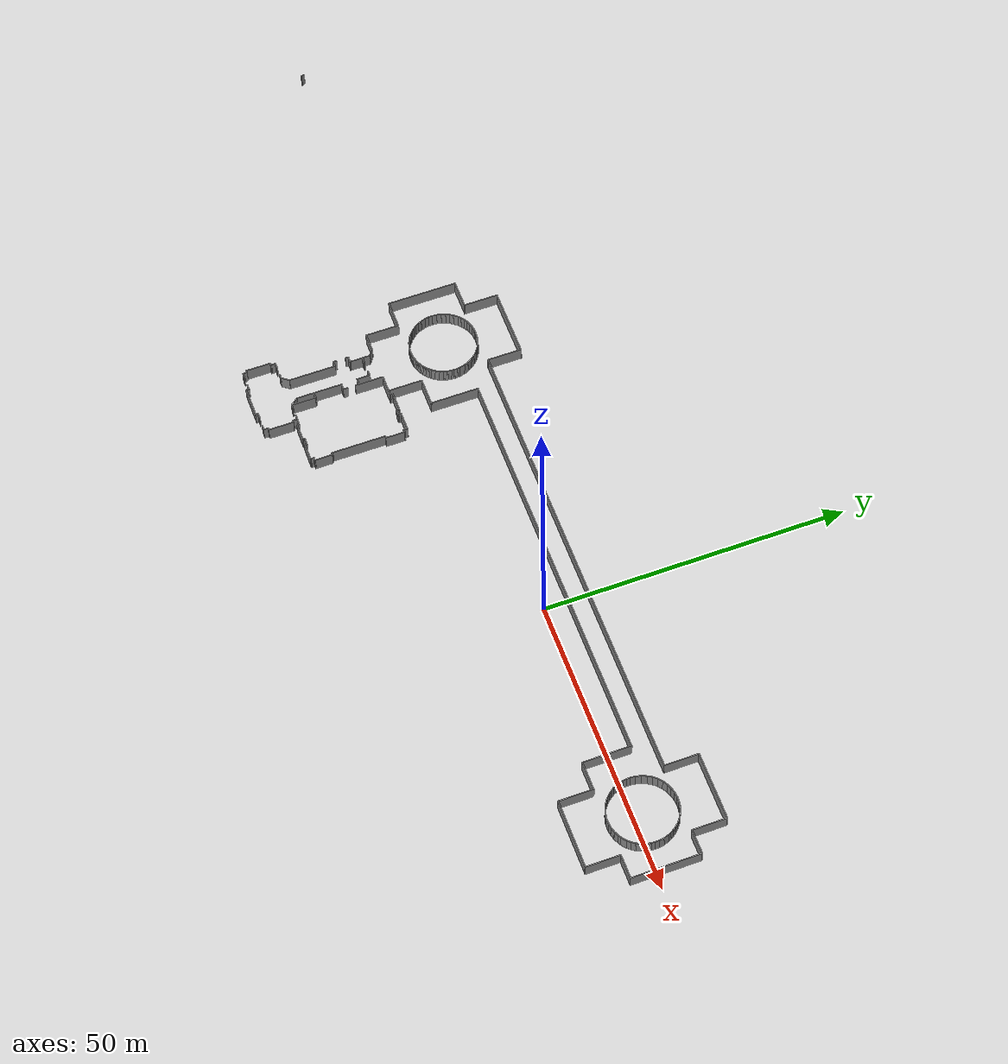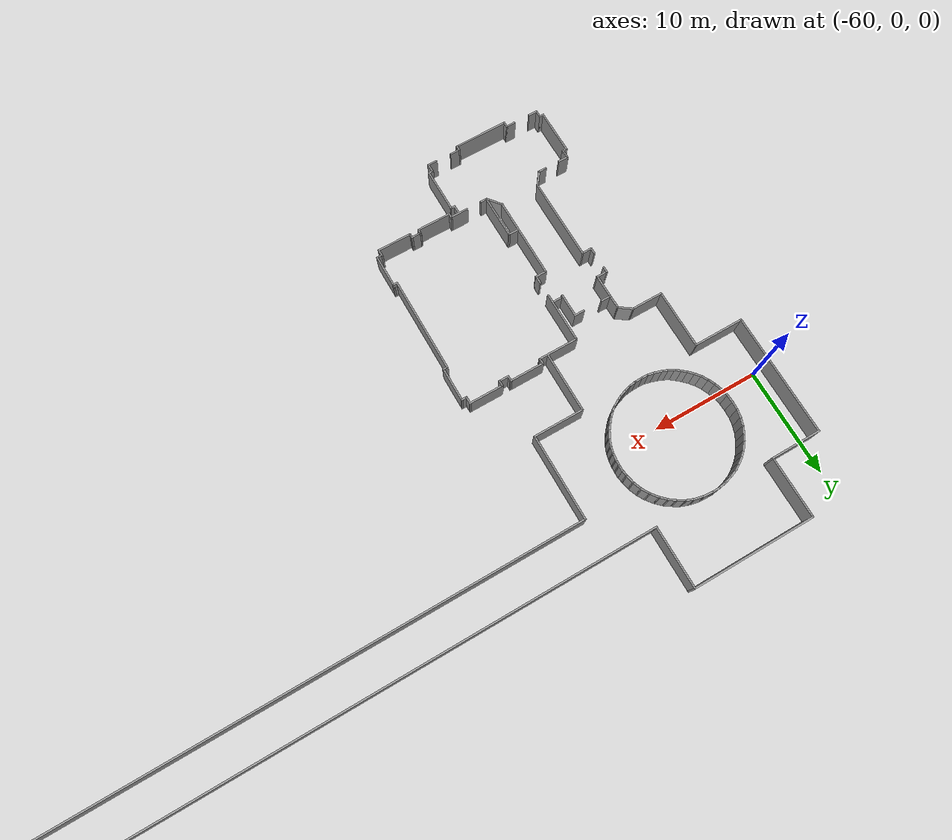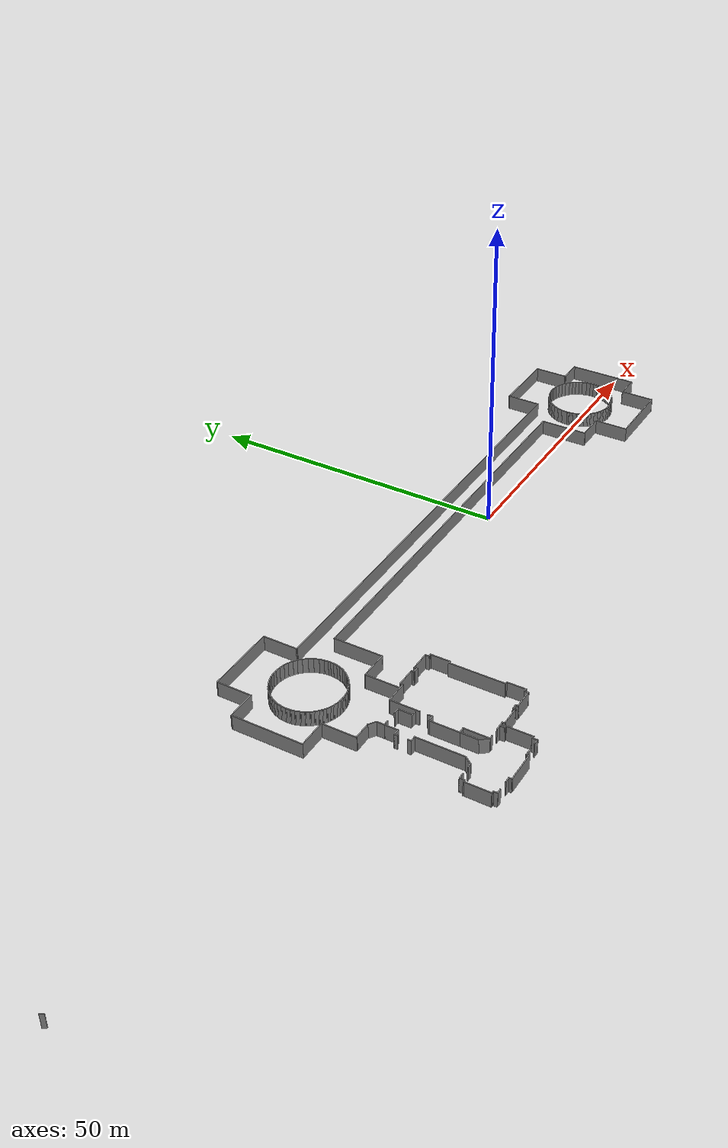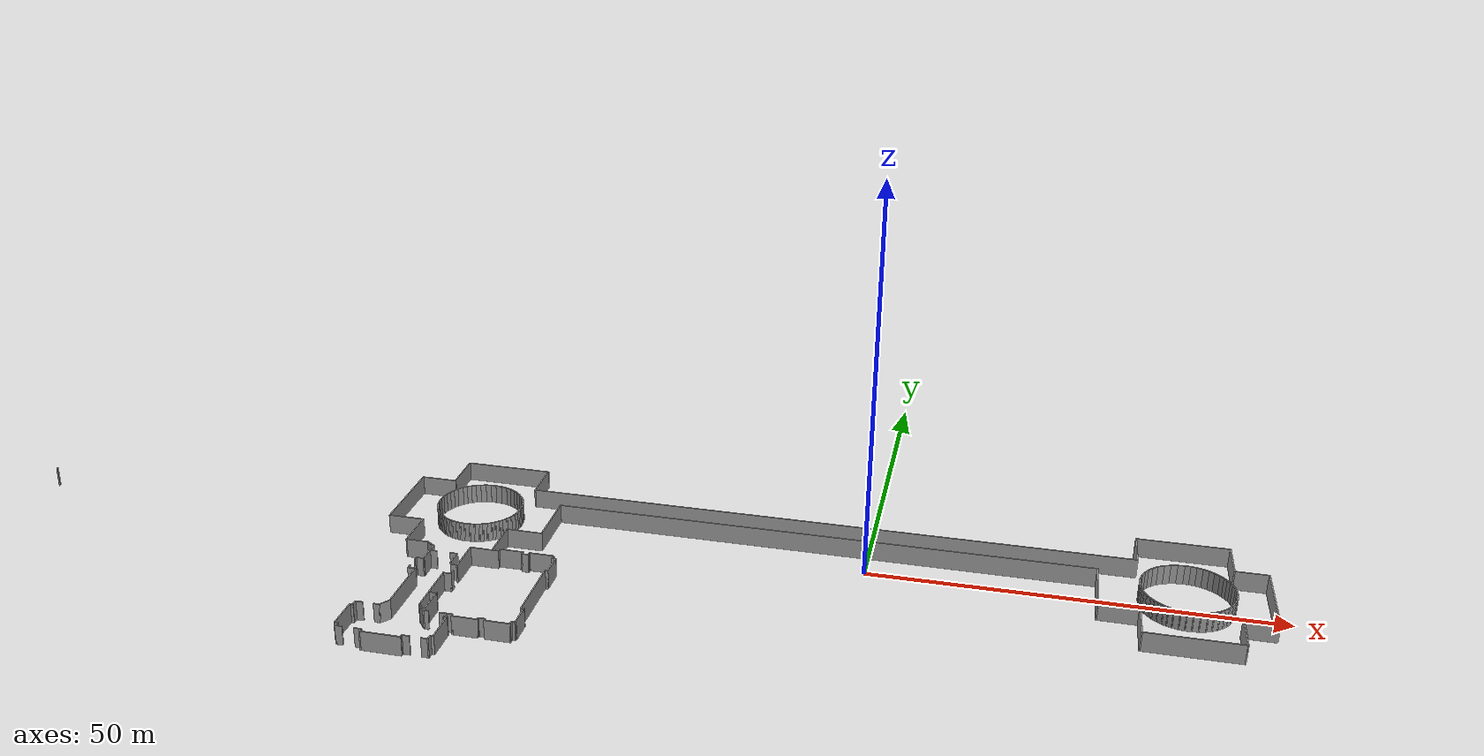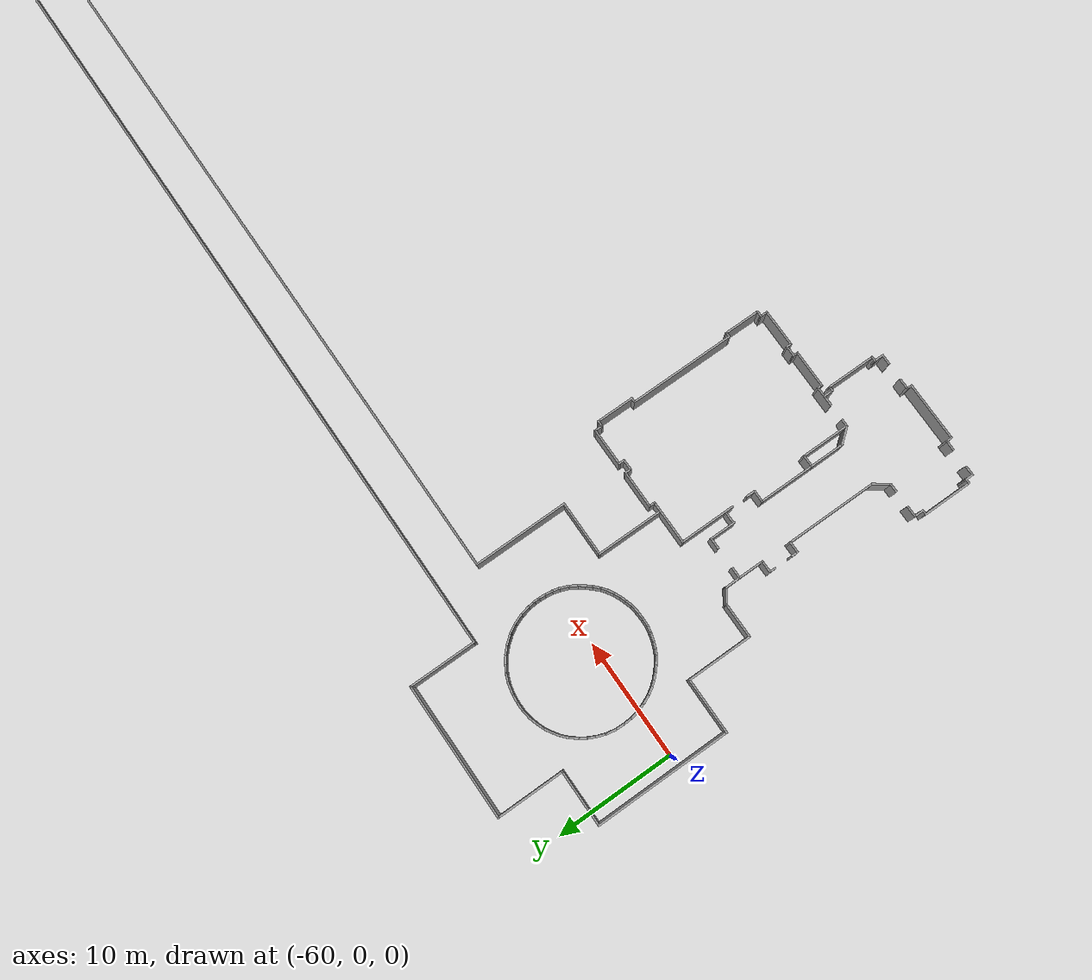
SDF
<?xml version='1.0'?>
<sdf version='1.7'>
  <model name='TD1_large'>
    <pose>-31.5443 -9.14138 0 0 -0 0</pose>
    <link name='Wall_109'>
      <collision name='Wall_109_Collision'>
        <geometry>
          <box>
            <size>3 0.15 2.5</size>
          </box>
        </geometry>
        <pose>0 0 1.25 0 -0 0</pose>
      </collision>
      <visual name='Wall_109_Visual'>
        <pose>0 0 1.25 0 -0 0</pose>
        <geometry>
          <box>
            <size>3 0.15 2.5</size>
          </box>
        </geometry>
        <material>
          <script>
            <uri>file://media/materials/scripts/gazebo.material</uri>
            <name>Gazebo/Grey</name>
          </script>
          <ambient>1 1 1 1</ambient>
        </material>
        <meta>
          <layer>0</layer>
        </meta>
      </visual>
      <pose>-17.17 -13.344 0 0 -0 -1.5708</pose>
    </link>
    <link name='Wall_11'>
      <collision name='Wall_11_Collision'>
        <geometry>
          <box>
            <size>1.75 0.15 2.5</size>
          </box>
        </geometry>
        <pose>0 0 1.25 0 -0 0</pose>
      </collision>
      <visual name='Wall_11_Visual'>
        <pose>0 0 1.25 0 -0 0</pose>
        <geometry>
          <box>
            <size>1.75 0.15 2.5</size>
          </box>
        </geometry>
        <material>
          <script>
            <uri>file://media/materials/scripts/gazebo.material</uri>
            <name>Gazebo/Grey</name>
          </script>
          <ambient>1 1 1 1</ambient>
        </material>
        <meta>
          <layer>0</layer>
        </meta>
      </visual>
      <pose>-13.4197 -15.9287 0 0 -0 -4.8e-05</pose>
    </link>
    <link name='Wall_112'>
      <collision name='Wall_112_Collision'>
        <geometry>
          <box>
            <size>1.57435 0.15 2.5</size>
          </box>
        </geometry>
        <pose>0 0 1.25 0 -0 0</pose>
      </collision>
      <visual name='Wall_112_Visual'>
        <pose>0 0 1.25 0 -0 0</pose>
        <geometry>
          <box>
            <size>1.57435 0.15 2.5</size>
          </box>
        </geometry>
        <material>
          <script>
            <uri>file://media/materials/scripts/gazebo.material</uri>
            <name>Gazebo/Grey</name>
          </script>
          <ambient>1 1 1 1</ambient>
        </material>
        <meta>
          <layer>0</layer>
        </meta>
      </visual>
      <pose>-16.7269 -15.3266 0 0 -0 -0.899319</pose>
    </link>
    <link name='Wall_115'>
      <collision name='Wall_115_Collision'>
        <geometry>
          <box>
            <size>0.812514 0.15 2.5</size>
          </box>
        </geometry>
        <pose>0 0 1.25 0 -0 0</pose>
      </collision>
      <visual name='Wall_115_Visual'>
        <pose>0 0 1.25 0 -0 0</pose>
        <geometry>
          <box>
            <size>0.812514 0.15 2.5</size>
          </box>
        </geometry>
        <material>
          <script>
            <uri>file://media/materials/scripts/gazebo.material</uri>
            <name>Gazebo/Grey</name>
          </script>
          <ambient>1 1 1 1</ambient>
        </material>
        <meta>
          <layer>0</layer>
        </meta>
      </visual>
      <pose>-22.0285 -15.9422 0 0 -0 0.008254</pose>
    </link>
    <link name='Wall_119'>
      <collision name='Wall_119_Collision'>
        <geometry>
          <box>
            <size>7.75 0.15 2.5</size>
          </box>
        </geometry>
        <pose>0 0 1.25 0 -0 0</pose>
      </collision>
      <visual name='Wall_119_Visual'>
        <pose>0 0 1.25 0 -0 0</pose>
        <geometry>
          <box>
            <size>7.75 0.15 2.5</size>
          </box>
        </geometry>
        <material>
          <script>
            <uri>file://media/materials/scripts/gazebo.material</uri>
            <name>Gazebo/Grey</name>
          </script>
          <ambient>1 1 1 1</ambient>
        </material>
        <meta>
          <layer>0</layer>
        </meta>
      </visual>
      <pose>-20.8577 -10.9663 0 0 -0 -1.5708</pose>
    </link>
    <link name='Wall_12'>
      <collision name='Wall_12_Collision'>
        <geometry>
          <box>
            <size>0.5 0.15 2.5</size>
          </box>
        </geometry>
        <pose>0 0 1.25 0 -0 0</pose>
      </collision>
      <visual name='Wall_12_Visual'>
        <pose>0 0 1.25 0 -0 0</pose>
        <geometry>
          <box>
            <size>0.5 0.15 2.5</size>
          </box>
        </geometry>
        <material>
          <script>
            <uri>file://media/materials/scripts/gazebo.material</uri>
            <name>Gazebo/Grey</name>
          </script>
          <ambient>1 1 1 1</ambient>
        </material>
        <meta>
          <layer>0</layer>
        </meta>
      </visual>
      <pose>-12.6196 -16.1037 0 0 -0 -1.5708</pose>
    </link>
    <link name='Wall_124'>
      <collision name='Wall_124_Collision'>
        <geometry>
          <box>
            <size>1.50767 0.15 2.5</size>
          </box>
        </geometry>
        <pose>0 0 1.25 0 -0 0</pose>
      </collision>
      <visual name='Wall_124_Visual'>
        <pose>0 0 1.25 0 -0 0</pose>
        <geometry>
          <box>
            <size>1.50767 0.15 2.5</size>
          </box>
        </geometry>
        <material>
          <script>
            <uri>file://media/materials/scripts/gazebo.material</uri>
            <name>Gazebo/Grey</name>
          </script>
          <ambient>1 1 1 1</ambient>
        </material>
        <meta>
          <layer>0</layer>
        </meta>
      </visual>
      <pose>-21.2899 -15.3964 0 0 -0 0.927295</pose>
    </link>
    <link name='Wall_128'>
      <collision name='Wall_128_Collision'>
        <geometry>
          <box>
            <size>1 0.15 2.5</size>
          </box>
        </geometry>
        <pose>0 0 1.25 0 -0 0</pose>
      </collision>
      <visual name='Wall_128_Visual'>
        <pose>0 0 1.25 0 -0 0</pose>
        <geometry>
          <box>
            <size>1 0.15 2.5</size>
          </box>
        </geometry>
        <material>
          <script>
            <uri>file://media/materials/scripts/gazebo.material</uri>
            <name>Gazebo/Grey</name>
          </script>
          <ambient>1 1 1 1</ambient>
        </material>
        <meta>
          <layer>0</layer>
        </meta>
      </visual>
      <pose>-24.2347 -15.945 0 0 -0 3.14159</pose>
    </link>
    <link name='Wall_129'>
      <collision name='Wall_129_Collision'>
        <geometry>
          <box>
            <size>0.9 0.15 2.5</size>
          </box>
        </geometry>
        <pose>0 0 1.25 0 -0 0</pose>
      </collision>
      <visual name='Wall_129_Visual'>
        <pose>0 0 1.25 0 -0 0</pose>
        <geometry>
          <box>
            <size>0.9 0.15 2.5</size>
          </box>
        </geometry>
        <material>
          <script>
            <uri>file://media/materials/scripts/gazebo.material</uri>
            <name>Gazebo/Grey</name>
          </script>
          <ambient>1 1 1 1</ambient>
        </material>
        <meta>
          <layer>0</layer>
        </meta>
      </visual>
      <pose>-24.6597 -16.32 0 0 -0 -1.5708</pose>
    </link>
    <link name='Wall_13'>
      <collision name='Wall_13_Collision'>
        <geometry>
          <box>
            <size>3.25 0.15 2.5</size>
          </box>
        </geometry>
        <pose>0 0 1.25 0 -0 0</pose>
      </collision>
      <visual name='Wall_13_Visual'>
        <pose>0 0 1.25 0 -0 0</pose>
        <geometry>
          <box>
            <size>3.25 0.15 2.5</size>
          </box>
        </geometry>
        <material>
          <script>
            <uri>file://media/materials/scripts/gazebo.material</uri>
            <name>Gazebo/Grey</name>
          </script>
          <ambient>1 1 1 1</ambient>
        </material>
        <meta>
          <layer>0</layer>
        </meta>
      </visual>
      <pose>-11.0696 -16.2787 0 0 -0 0</pose>
    </link>
    <link name='Wall_131'>
      <collision name='Wall_131_Collision'>
        <geometry>
          <box>
            <size>0.5 0.15 2.5</size>
          </box>
        </geometry>
        <pose>0 0 1.25 0 -0 0</pose>
      </collision>
      <visual name='Wall_131_Visual'>
        <pose>0 0 1.25 0 -0 0</pose>
        <geometry>
          <box>
            <size>0.5 0.15 2.5</size>
          </box>
        </geometry>
        <material>
          <script>
            <uri>file://media/materials/scripts/gazebo.material</uri>
            <name>Gazebo/Grey</name>
          </script>
          <ambient>1 1 1 1</ambient>
        </material>
        <meta>
          <layer>0</layer>
        </meta>
      </visual>
      <pose>-24.8347 -16.695 0 0 -0 3.14159</pose>
    </link>
    <link name='Wall_133'>
      <collision name='Wall_133_Collision'>
        <geometry>
          <box>
            <size>4.25 0.15 2.5</size>
          </box>
        </geometry>
        <pose>0 0 1.25 0 -0 0</pose>
      </collision>
      <visual name='Wall_133_Visual'>
        <pose>0 0 1.25 0 -0 0</pose>
        <geometry>
          <box>
            <size>4.25 0.15 2.5</size>
          </box>
        </geometry>
        <material>
          <script>
            <uri>file://media/materials/scripts/gazebo.material</uri>
            <name>Gazebo/Grey</name>
          </script>
          <ambient>1 1 1 1</ambient>
        </material>
        <meta>
          <layer>0</layer>
        </meta>
      </visual>
      <pose>-25.0097 -18.745 0 0 -0 -1.5708</pose>
    </link>
    <link name='Wall_134'>
      <collision name='Wall_134_Collision'>
        <geometry>
          <box>
            <size>0.5 0.15 2.5</size>
          </box>
        </geometry>
        <pose>0 0 1.25 0 -0 0</pose>
      </collision>
      <visual name='Wall_134_Visual'>
        <pose>0 0 1.25 0 -0 0</pose>
        <geometry>
          <box>
            <size>0.5 0.15 2.5</size>
          </box>
        </geometry>
        <material>
          <script>
            <uri>file://media/materials/scripts/gazebo.material</uri>
            <name>Gazebo/Grey</name>
          </script>
          <ambient>1 1 1 1</ambient>
        </material>
        <meta>
          <layer>0</layer>
        </meta>
      </visual>
      <pose>-24.8347 -20.795 0 0 -0 0</pose>
    </link>
    <link name='Wall_135'>
      <collision name='Wall_135_Collision'>
        <geometry>
          <box>
            <size>0.75 0.15 2.5</size>
          </box>
        </geometry>
        <pose>0 0 1.25 0 -0 0</pose>
      </collision>
      <visual name='Wall_135_Visual'>
        <pose>0 0 1.25 0 -0 0</pose>
        <geometry>
          <box>
            <size>0.75 0.15 2.5</size>
          </box>
        </geometry>
        <material>
          <script>
            <uri>file://media/materials/scripts/gazebo.material</uri>
            <name>Gazebo/Grey</name>
          </script>
          <ambient>1 1 1 1</ambient>
        </material>
        <meta>
          <layer>0</layer>
        </meta>
      </visual>
      <pose>-24.6597 -21.095 0 0 -0 -1.5708</pose>
    </link>
    <link name='Wall_136'>
      <collision name='Wall_136_Collision'>
        <geometry>
          <box>
            <size>0.9 0.15 2.5</size>
          </box>
        </geometry>
        <pose>0 0 1.25 0 -0 0</pose>
      </collision>
      <visual name='Wall_136_Visual'>
        <pose>0 0 1.25 0 -0 0</pose>
        <geometry>
          <box>
            <size>0.9 0.15 2.5</size>
          </box>
        </geometry>
        <material>
          <script>
            <uri>file://media/materials/scripts/gazebo.material</uri>
            <name>Gazebo/Grey</name>
          </script>
          <ambient>1 1 1 1</ambient>
        </material>
        <meta>
          <layer>0</layer>
        </meta>
      </visual>
      <pose>-24.2847 -21.395 0 0 -0 0</pose>
    </link>
    <link name='Wall_14'>
      <collision name='Wall_14_Collision'>
        <geometry>
          <box>
            <size>0.5 0.15 2.5</size>
          </box>
        </geometry>
        <pose>0 0 1.25 0 -0 0</pose>
      </collision>
      <visual name='Wall_14_Visual'>
        <pose>0 0 1.25 0 -0 0</pose>
        <geometry>
          <box>
            <size>0.5 0.15 2.5</size>
          </box>
        </geometry>
        <material>
          <script>
            <uri>file://media/materials/scripts/gazebo.material</uri>
            <name>Gazebo/Grey</name>
          </script>
          <ambient>1 1 1 1</ambient>
        </material>
        <meta>
          <layer>0</layer>
        </meta>
      </visual>
      <pose>-9.51964 -16.1037 0 0 -0 1.5708</pose>
    </link>
    <link name='Wall_141'>
      <collision name='Wall_141_Collision'>
        <geometry>
          <box>
            <size>0.95 0.15 2.5</size>
          </box>
        </geometry>
        <pose>0 0 1.25 0 -0 0</pose>
      </collision>
      <visual name='Wall_141_Visual'>
        <pose>0 0 1.25 0 -0 0</pose>
        <geometry>
          <box>
            <size>0.95 0.15 2.5</size>
          </box>
        </geometry>
        <material>
          <script>
            <uri>file://media/materials/scripts/gazebo.material</uri>
            <name>Gazebo/Grey</name>
          </script>
          <ambient>1 1 1 1</ambient>
        </material>
        <meta>
          <layer>0</layer>
        </meta>
      </visual>
      <pose>-21.9097 -21.395 0 0 -0 0</pose>
    </link>
    <link name='Wall_143'>
      <collision name='Wall_143_Collision'>
        <geometry>
          <box>
            <size>0.6 0.15 2.5</size>
          </box>
        </geometry>
        <pose>0 0 1.25 0 -0 0</pose>
      </collision>
      <visual name='Wall_143_Visual'>
        <pose>0 0 1.25 0 -0 0</pose>
        <geometry>
          <box>
            <size>0.6 0.15 2.5</size>
          </box>
        </geometry>
        <material>
          <script>
            <uri>file://media/materials/scripts/gazebo.material</uri>
            <name>Gazebo/Grey</name>
          </script>
          <ambient>1 1 1 1</ambient>
        </material>
        <meta>
          <layer>0</layer>
        </meta>
      </visual>
      <pose>-21.5097 -21.62 0 0 -0 -1.5708</pose>
    </link>
    <link name='Wall_145'>
      <collision name='Wall_145_Collision'>
        <geometry>
          <box>
            <size>5.1 0.15 2.5</size>
          </box>
        </geometry>
        <pose>0 0 1.25 0 -0 0</pose>
      </collision>
      <visual name='Wall_145_Visual'>
        <pose>0 0 1.25 0 -0 0</pose>
        <geometry>
          <box>
            <size>5.1 0.15 2.5</size>
          </box>
        </geometry>
        <material>
          <script>
            <uri>file://media/materials/scripts/gazebo.material</uri>
            <name>Gazebo/Grey</name>
          </script>
          <ambient>1 1 1 1</ambient>
        </material>
        <meta>
          <layer>0</layer>
        </meta>
      </visual>
      <pose>-19.0347 -21.8448 0 0 -0 7.1e-05</pose>
    </link>
    <link name='Wall_147'>
      <collision name='Wall_147_Collision'>
        <geometry>
          <box>
            <size>0.55 0.15 2.5</size>
          </box>
        </geometry>
        <pose>0 0 1.25 0 -0 0</pose>
      </collision>
      <visual name='Wall_147_Visual'>
        <pose>0 0 1.25 0 -0 0</pose>
        <geometry>
          <box>
            <size>0.55 0.15 2.5</size>
          </box>
        </geometry>
        <material>
          <script>
            <uri>file://media/materials/scripts/gazebo.material</uri>
            <name>Gazebo/Grey</name>
          </script>
          <ambient>1 1 1 1</ambient>
        </material>
        <meta>
          <layer>0</layer>
        </meta>
      </visual>
      <pose>-16.5597 -21.6446 0 0 -0 1.5708</pose>
    </link>
    <link name='Wall_149'>
      <collision name='Wall_149_Collision'>
        <geometry>
          <box>
            <size>1 0.15 2.5</size>
          </box>
        </geometry>
        <pose>0 0 1.25 0 -0 0</pose>
      </collision>
      <visual name='Wall_149_Visual'>
        <pose>0 0 1.25 0 -0 0</pose>
        <geometry>
          <box>
            <size>1 0.15 2.5</size>
          </box>
        </geometry>
        <material>
          <script>
            <uri>file://media/materials/scripts/gazebo.material</uri>
            <name>Gazebo/Grey</name>
          </script>
          <ambient>1 1 1 1</ambient>
        </material>
        <meta>
          <layer>0</layer>
        </meta>
      </visual>
      <pose>-16.1347 -21.4446 0 0 -0 0</pose>
    </link>
    <link name='Wall_15'>
      <collision name='Wall_15_Collision'>
        <geometry>
          <box>
            <size>1 0.15 2.5</size>
          </box>
        </geometry>
        <pose>0 0 1.25 0 -0 0</pose>
      </collision>
      <visual name='Wall_15_Visual'>
        <pose>0 0 1.25 0 -0 0</pose>
        <geometry>
          <box>
            <size>1 0.15 2.5</size>
          </box>
        </geometry>
        <material>
          <script>
            <uri>file://media/materials/scripts/gazebo.material</uri>
            <name>Gazebo/Grey</name>
          </script>
          <ambient>1 1 1 1</ambient>
        </material>
        <meta>
          <layer>0</layer>
        </meta>
      </visual>
      <pose>-9.09464 -15.9287 0 0 -0 0</pose>
    </link>
    <link name='Wall_152'>
      <collision name='Wall_152_Collision'>
        <geometry>
          <box>
            <size>0.9 0.15 2.5</size>
          </box>
        </geometry>
        <pose>0 0 1.25 0 -0 0</pose>
      </collision>
      <visual name='Wall_152_Visual'>
        <pose>0 0 1.25 0 -0 0</pose>
        <geometry>
          <box>
            <size>0.9 0.15 2.5</size>
          </box>
        </geometry>
        <material>
          <script>
            <uri>file://media/materials/scripts/gazebo.material</uri>
            <name>Gazebo/Grey</name>
          </script>
          <ambient>1 1 1 1</ambient>
        </material>
        <meta>
          <layer>0</layer>
        </meta>
      </visual>
      <pose>-13.8239 -21.4826 0 0 -0 0</pose>
    </link>
    <link name='Wall_155'>
      <collision name='Wall_155_Collision'>
        <geometry>
          <box>
            <size>0.5 0.15 2.5</size>
          </box>
        </geometry>
        <pose>0 0 1.25 0 -0 0</pose>
      </collision>
      <visual name='Wall_155_Visual'>
        <pose>0 0 1.25 0 -0 0</pose>
        <geometry>
          <box>
            <size>0.5 0.15 2.5</size>
          </box>
        </geometry>
        <material>
          <script>
            <uri>file://media/materials/scripts/gazebo.material</uri>
            <name>Gazebo/Grey</name>
          </script>
          <ambient>1 1 1 1</ambient>
        </material>
        <meta>
          <layer>0</layer>
        </meta>
      </visual>
      <pose>-13.2347 -20.7446 0 0 -0 0</pose>
    </link>
    <link name='Wall_157'>
      <collision name='Wall_157_Collision'>
        <geometry>
          <box>
            <size>0.9 0.15 2.5</size>
          </box>
        </geometry>
        <pose>0 0 1.25 0 -0 0</pose>
      </collision>
      <visual name='Wall_157_Visual'>
        <pose>0 0 1.25 0 -0 0</pose>
        <geometry>
          <box>
            <size>0.9 0.15 2.5</size>
          </box>
        </geometry>
        <material>
          <script>
            <uri>file://media/materials/scripts/gazebo.material</uri>
            <name>Gazebo/Grey</name>
          </script>
          <ambient>1 1 1 1</ambient>
        </material>
        <meta>
          <layer>0</layer>
        </meta>
      </visual>
      <pose>-13.4097 -21.1196 0 0 -0 -1.5708</pose>
    </link>
    <link name='Wall_159'>
      <collision name='Wall_159_Collision'>
        <geometry>
          <box>
            <size>4.2 0.15 2.5</size>
          </box>
        </geometry>
        <pose>0 0 1.25 0 -0 0</pose>
      </collision>
      <visual name='Wall_159_Visual'>
        <pose>0 0 1.25 0 -0 0</pose>
        <geometry>
          <box>
            <size>4.2 0.15 2.5</size>
          </box>
        </geometry>
        <material>
          <script>
            <uri>file://media/materials/scripts/gazebo.material</uri>
            <name>Gazebo/Grey</name>
          </script>
          <ambient>1 1 1 1</ambient>
        </material>
        <meta>
          <layer>0</layer>
        </meta>
      </visual>
      <pose>-13.0597 -18.7196 0 0 -0 1.5708</pose>
    </link>
    <link name='Wall_16'>
      <collision name='Wall_16_Collision'>
        <geometry>
          <box>
            <size>0.5 0.15 2.5</size>
          </box>
        </geometry>
        <pose>0 0 1.25 0 -0 0</pose>
      </collision>
      <visual name='Wall_16_Visual'>
        <pose>0 0 1.25 0 -0 0</pose>
        <geometry>
          <box>
            <size>0.5 0.15 2.5</size>
          </box>
        </geometry>
        <material>
          <script>
            <uri>file://media/materials/scripts/gazebo.material</uri>
            <name>Gazebo/Grey</name>
          </script>
          <ambient>1 1 1 1</ambient>
        </material>
        <meta>
          <layer>0</layer>
        </meta>
      </visual>
      <pose>-8.66964 -16.1037 0 0 -0 -1.5708</pose>
    </link>
    <link name='Wall_161'>
      <collision name='Wall_161_Collision'>
        <geometry>
          <box>
            <size>0.5 0.15 2.5</size>
          </box>
        </geometry>
        <pose>0 0 1.25 0 -0 0</pose>
      </collision>
      <visual name='Wall_161_Visual'>
        <pose>0 0 1.25 0 -0 0</pose>
        <geometry>
          <box>
            <size>0.5 0.15 2.5</size>
          </box>
        </geometry>
        <material>
          <script>
            <uri>file://media/materials/scripts/gazebo.material</uri>
            <name>Gazebo/Grey</name>
          </script>
          <ambient>1 1 1 1</ambient>
        </material>
        <meta>
          <layer>0</layer>
        </meta>
      </visual>
      <pose>-13.2347 -16.6946 0 0 -0 3.14159</pose>
    </link>
    <link name='Wall_162'>
      <collision name='Wall_162_Collision'>
        <geometry>
          <box>
            <size>0.9 0.15 2.5</size>
          </box>
        </geometry>
        <pose>0 0 1.25 0 -0 0</pose>
      </collision>
      <visual name='Wall_162_Visual'>
        <pose>0 0 1.25 0 -0 0</pose>
        <geometry>
          <box>
            <size>0.9 0.15 2.5</size>
          </box>
        </geometry>
        <material>
          <script>
            <uri>file://media/materials/scripts/gazebo.material</uri>
            <name>Gazebo/Grey</name>
          </script>
          <ambient>1 1 1 1</ambient>
        </material>
        <meta>
          <layer>0</layer>
        </meta>
      </visual>
      <pose>-13.4097 -16.3196 0 0 -0 1.5708</pose>
    </link>
    <link name='Wall_164'>
      <collision name='Wall_164_Collision'>
        <geometry>
          <box>
            <size>5.6 0.15 2.5</size>
          </box>
        </geometry>
        <pose>0 0 1.25 0 -0 0</pose>
      </collision>
      <visual name='Wall_164_Visual'>
        <pose>0 0 1.25 0 -0 0</pose>
        <geometry>
          <box>
            <size>5.6 0.15 2.5</size>
          </box>
        </geometry>
        <material>
          <script>
            <uri>file://media/materials/scripts/gazebo.material</uri>
            <name>Gazebo/Grey</name>
          </script>
          <ambient>1 1 1 1</ambient>
        </material>
        <meta>
          <layer>0</layer>
        </meta>
      </visual>
      <pose>-13.3873 2.23327 0 0 -0 -1.5708</pose>
    </link>
    <link name='Wall_166'>
      <collision name='Wall_166_Collision'>
        <geometry>
          <box>
            <size>4.75 0.15 2.5</size>
          </box>
        </geometry>
        <pose>0 0 1.25 0 -0 0</pose>
      </collision>
      <visual name='Wall_166_Visual'>
        <pose>0 0 1.25 0 -0 0</pose>
        <geometry>
          <box>
            <size>4.75 0.15 2.5</size>
          </box>
        </geometry>
        <material>
          <script>
            <uri>file://media/materials/scripts/gazebo.material</uri>
            <name>Gazebo/Grey</name>
          </script>
          <ambient>1 1 1 1</ambient>
        </material>
        <meta>
          <layer>0</layer>
        </meta>
      </visual>
      <pose>-11.0873 4.95827 0 0 -0 0</pose>
    </link>
    <link name='Wall_168'>
      <collision name='Wall_168_Collision'>
        <geometry>
          <box>
            <size>8.05 0.15 2.5</size>
          </box>
        </geometry>
        <pose>0 0 1.25 0 -0 0</pose>
      </collision>
      <visual name='Wall_168_Visual'>
        <pose>0 0 1.25 0 -0 0</pose>
        <geometry>
          <box>
            <size>8.05 0.15 2.5</size>
          </box>
        </geometry>
        <material>
          <script>
            <uri>file://media/materials/scripts/gazebo.material</uri>
            <name>Gazebo/Grey</name>
          </script>
          <ambient>1 1 1 1</ambient>
        </material>
        <meta>
          <layer>0</layer>
        </meta>
      </visual>
      <pose>-8.78731 8.90827 0 0 -0 1.5708</pose>
    </link>
    <link name='Wall_17'>
      <collision name='Wall_17_Collision'>
        <geometry>
          <box>
            <size>3.25 0.15 2.5</size>
          </box>
        </geometry>
        <pose>0 0 1.25 0 -0 0</pose>
      </collision>
      <visual name='Wall_17_Visual'>
        <pose>0 0 1.25 0 -0 0</pose>
        <geometry>
          <box>
            <size>3.25 0.15 2.5</size>
          </box>
        </geometry>
        <material>
          <script>
            <uri>file://media/materials/scripts/gazebo.material</uri>
            <name>Gazebo/Grey</name>
          </script>
          <ambient>1 1 1 1</ambient>
        </material>
        <meta>
          <layer>0</layer>
        </meta>
      </visual>
      <pose>-7.11964 -16.2787 0 0 -0 0</pose>
    </link>
    <link name='Wall_171'>
      <collision name='Wall_171_Collision'>
        <geometry>
          <box>
            <size>68.1 0.15 2.5</size>
          </box>
        </geometry>
        <pose>0 0 1.25 0 -0 0</pose>
      </collision>
      <visual name='Wall_171_Visual'>
        <pose>0 0 1.25 0 -0 0</pose>
        <geometry>
          <box>
            <size>68.1 0.15 2.5</size>
          </box>
        </geometry>
        <material>
          <script>
            <uri>file://media/materials/scripts/gazebo.material</uri>
            <name>Gazebo/Grey</name>
          </script>
          <ambient>1 1 1 1</ambient>
        </material>
        <meta>
          <layer>0</layer>
        </meta>
      </visual>
      <pose>25.1877 12.8583 0 0 -0 0</pose>
    </link>
    <link name='Wall_173'>
      <collision name='Wall_173_Collision'>
        <geometry>
          <box>
            <size>8 0.15 2.5</size>
          </box>
        </geometry>
        <pose>0 0 1.25 0 -0 0</pose>
      </collision>
      <visual name='Wall_173_Visual'>
        <pose>0 0 1.25 0 -0 0</pose>
        <geometry>
          <box>
            <size>8 0.15 2.5</size>
          </box>
        </geometry>
        <material>
          <script>
            <uri>file://media/materials/scripts/gazebo.material</uri>
            <name>Gazebo/Grey</name>
          </script>
          <ambient>1 1 1 1</ambient>
        </material>
        <meta>
          <layer>0</layer>
        </meta>
      </visual>
      <pose>59.1627 8.93327 0 0 -0 -1.5708</pose>
    </link>
    <link name='Wall_174'>
      <collision name='Wall_174_Collision'>
        <geometry>
          <box>
            <size>4.85 0.15 2.5</size>
          </box>
        </geometry>
        <pose>0 0 1.25 0 -0 0</pose>
      </collision>
      <visual name='Wall_174_Visual'>
        <pose>0 0 1.25 0 -0 0</pose>
        <geometry>
          <box>
            <size>4.85 0.15 2.5</size>
          </box>
        </geometry>
        <material>
          <script>
            <uri>file://media/materials/scripts/gazebo.material</uri>
            <name>Gazebo/Grey</name>
          </script>
          <ambient>1 1 1 1</ambient>
        </material>
        <meta>
          <layer>0</layer>
        </meta>
      </visual>
      <pose>61.5127 5.00827 0 0 -0 0</pose>
    </link>
    <link name='Wall_179'>
      <collision name='Wall_179_Collision'>
        <geometry>
          <box>
            <size>5.75 0.15 2.5</size>
          </box>
        </geometry>
        <pose>0 0 1.25 0 -0 0</pose>
      </collision>
      <visual name='Wall_179_Visual'>
        <pose>0 0 1.25 0 -0 0</pose>
        <geometry>
          <box>
            <size>5.75 0.15 2.5</size>
          </box>
        </geometry>
        <material>
          <script>
            <uri>file://media/materials/scripts/gazebo.material</uri>
            <name>Gazebo/Grey</name>
          </script>
          <ambient>1 1 1 1</ambient>
        </material>
        <meta>
          <layer>0</layer>
        </meta>
      </visual>
      <pose>63.8627 2.20827 0 0 -0 -1.5708</pose>
    </link>
    <link name='Wall_18'>
      <collision name='Wall_18_Collision'>
        <geometry>
          <box>
            <size>0.7 0.15 2.5</size>
          </box>
        </geometry>
        <pose>0 0 1.25 0 -0 0</pose>
      </collision>
      <visual name='Wall_18_Visual'>
        <pose>0 0 1.25 0 -0 0</pose>
        <geometry>
          <box>
            <size>0.7 0.15 2.5</size>
          </box>
        </geometry>
        <material>
          <script>
            <uri>file://media/materials/scripts/gazebo.material</uri>
            <name>Gazebo/Grey</name>
          </script>
          <ambient>1 1 1 1</ambient>
        </material>
        <meta>
          <layer>0</layer>
        </meta>
      </visual>
      <pose>-5.56964 -16.0037 0 0 -0 1.5708</pose>
    </link>
    <link name='Wall_180'>
      <collision name='Wall_180_Collision'>
        <geometry>
          <box>
            <size>11.5 0.15 2.5</size>
          </box>
        </geometry>
        <pose>0 0 1.25 0 -0 0</pose>
      </collision>
      <visual name='Wall_180_Visual'>
        <pose>0 0 1.25 0 -0 0</pose>
        <geometry>
          <box>
            <size>11.5 0.15 2.5</size>
          </box>
        </geometry>
        <material>
          <script>
            <uri>file://media/materials/scripts/gazebo.material</uri>
            <name>Gazebo/Grey</name>
          </script>
          <ambient>1 1 1 1</ambient>
        </material>
        <meta>
          <layer>0</layer>
        </meta>
      </visual>
      <pose>69.5377 -0.591726 0 0 -0 0</pose>
    </link>
    <link name='Wall_181'>
      <collision name='Wall_181_Collision'>
        <geometry>
          <box>
            <size>5.7 0.15 2.5</size>
          </box>
        </geometry>
        <pose>0 0 1.25 0 -0 0</pose>
      </collision>
      <visual name='Wall_181_Visual'>
        <pose>0 0 1.25 0 -0 0</pose>
        <geometry>
          <box>
            <size>5.7 0.15 2.5</size>
          </box>
        </geometry>
        <material>
          <script>
            <uri>file://media/materials/scripts/gazebo.material</uri>
            <name>Gazebo/Grey</name>
          </script>
          <ambient>1 1 1 1</ambient>
        </material>
        <meta>
          <layer>0</layer>
        </meta>
      </visual>
      <pose>75.2127 2.18327 0 0 -0 1.5708</pose>
    </link>
    <link name='Wall_183'>
      <collision name='Wall_183_Collision'>
        <geometry>
          <box>
            <size>4.1 0.15 2.5</size>
          </box>
        </geometry>
        <pose>0 0 1.25 0 -0 0</pose>
      </collision>
      <visual name='Wall_183_Visual'>
        <pose>0 0 1.25 0 -0 0</pose>
        <geometry>
          <box>
            <size>4.1 0.15 2.5</size>
          </box>
        </geometry>
        <material>
          <script>
            <uri>file://media/materials/scripts/gazebo.material</uri>
            <name>Gazebo/Grey</name>
          </script>
          <ambient>1 1 1 1</ambient>
        </material>
        <meta>
          <layer>0</layer>
        </meta>
      </visual>
      <pose>77.1877 4.95827 0 0 -0 0</pose>
    </link>
    <link name='Wall_185'>
      <collision name='Wall_185_Collision'>
        <geometry>
          <box>
            <size>11.4 0.15 2.5</size>
          </box>
        </geometry>
        <pose>0 0 1.25 0 -0 0</pose>
      </collision>
      <visual name='Wall_185_Visual'>
        <pose>0 0 1.25 0 -0 0</pose>
        <geometry>
          <box>
            <size>11.4 0.15 2.5</size>
          </box>
        </geometry>
        <material>
          <script>
            <uri>file://media/materials/scripts/gazebo.material</uri>
            <name>Gazebo/Grey</name>
          </script>
          <ambient>1 1 1 1</ambient>
        </material>
        <meta>
          <layer>0</layer>
        </meta>
      </visual>
      <pose>79.1627 10.5833 0 0 -0 1.5708</pose>
    </link>
    <link name='Wall_188'>
      <collision name='Wall_188_Collision'>
        <geometry>
          <box>
            <size>4.15 0.15 2.5</size>
          </box>
        </geometry>
        <pose>0 0 1.25 0 -0 0</pose>
      </collision>
      <visual name='Wall_188_Visual'>
        <pose>0 0 1.25 0 -0 0</pose>
        <geometry>
          <box>
            <size>4.15 0.15 2.5</size>
          </box>
        </geometry>
        <material>
          <script>
            <uri>file://media/materials/scripts/gazebo.material</uri>
            <name>Gazebo/Grey</name>
          </script>
          <ambient>1 1 1 1</ambient>
        </material>
        <meta>
          <layer>0</layer>
        </meta>
      </visual>
      <pose>77.1627 16.2083 0 0 -0 3.14159</pose>
    </link>
    <link name='Wall_190'>
      <collision name='Wall_190_Collision'>
        <geometry>
          <box>
            <size>5.7367 0.15 2.5</size>
          </box>
        </geometry>
        <pose>0 0 1.25 0 -0 0</pose>
      </collision>
      <visual name='Wall_190_Visual'>
        <pose>0 0 1.25 0 -0 0</pose>
        <geometry>
          <box>
            <size>5.7367 0.15 2.5</size>
          </box>
        </geometry>
        <material>
          <script>
            <uri>file://media/materials/scripts/gazebo.material</uri>
            <name>Gazebo/Grey</name>
          </script>
          <ambient>1 1 1 1</ambient>
        </material>
        <meta>
          <layer>0</layer>
        </meta>
      </visual>
      <pose>75.1627 19.0016 0 0 -0 1.5708</pose>
    </link>
    <link name='Wall_192'>
      <collision name='Wall_192_Collision'>
        <geometry>
          <box>
            <size>11.4 0.15 2.5</size>
          </box>
        </geometry>
        <pose>0 0 1.25 0 -0 0</pose>
      </collision>
      <visual name='Wall_192_Visual'>
        <pose>0 0 1.25 0 -0 0</pose>
        <geometry>
          <box>
            <size>11.4 0.15 2.5</size>
          </box>
        </geometry>
        <material>
          <script>
            <uri>file://media/materials/scripts/gazebo.material</uri>
            <name>Gazebo/Grey</name>
          </script>
          <ambient>1 1 1 1</ambient>
        </material>
        <meta>
          <layer>0</layer>
        </meta>
      </visual>
      <pose>69.5377 21.795 0 0 -0 3.14159</pose>
    </link>
    <link name='Wall_195'>
      <collision name='Wall_195_Collision'>
        <geometry>
          <box>
            <size>5.7 0.15 2.5</size>
          </box>
        </geometry>
        <pose>0 0 1.25 0 -0 0</pose>
      </collision>
      <visual name='Wall_195_Visual'>
        <pose>0 0 1.25 0 -0 0</pose>
        <geometry>
          <box>
            <size>5.7 0.15 2.5</size>
          </box>
        </geometry>
        <material>
          <script>
            <uri>file://media/materials/scripts/gazebo.material</uri>
            <name>Gazebo/Grey</name>
          </script>
          <ambient>1 1 1 1</ambient>
        </material>
        <meta>
          <layer>0</layer>
        </meta>
      </visual>
      <pose>63.9127 19.02 0 0 -0 -1.5708</pose>
    </link>
    <link name='Wall_197'>
      <collision name='Wall_197_Collision'>
        <geometry>
          <box>
            <size>77.45 0.15 2.5</size>
          </box>
        </geometry>
        <pose>0 0 1.25 0 -0 0</pose>
      </collision>
      <visual name='Wall_197_Visual'>
        <pose>0 0 1.25 0 -0 0</pose>
        <geometry>
          <box>
            <size>77.45 0.15 2.5</size>
          </box>
        </geometry>
        <material>
          <script>
            <uri>file://media/materials/scripts/gazebo.material</uri>
            <name>Gazebo/Grey</name>
          </script>
          <ambient>1 1 1 1</ambient>
        </material>
        <meta>
          <layer>0</layer>
        </meta>
      </visual>
      <pose>25.2627 16.245 0 0 -0 3.14159</pose>
    </link>
    <link name='Wall_20'>
      <collision name='Wall_20_Collision'>
        <geometry>
          <box>
            <size>0.6 0.15 2.5</size>
          </box>
        </geometry>
        <pose>0 0 1.25 0 -0 0</pose>
      </collision>
      <visual name='Wall_20_Visual'>
        <pose>0 0 1.25 0 -0 0</pose>
        <geometry>
          <box>
            <size>0.6 0.15 2.5</size>
          </box>
        </geometry>
        <material>
          <script>
            <uri>file://media/materials/scripts/gazebo.material</uri>
            <name>Gazebo/Grey</name>
          </script>
          <ambient>1 1 1 1</ambient>
        </material>
        <meta>
          <layer>0</layer>
        </meta>
      </visual>
      <pose>-5.34464 -15.7287 0 0 -0 0</pose>
    </link>
    <link name='Wall_200'>
      <collision name='Wall_200_Collision'>
        <geometry>
          <box>
            <size>5.75 0.15 2.5</size>
          </box>
        </geometry>
        <pose>0 0 1.25 0 -0 0</pose>
      </collision>
      <visual name='Wall_200_Visual'>
        <pose>0 0 1.25 0 -0 0</pose>
        <geometry>
          <box>
            <size>5.75 0.15 2.5</size>
          </box>
        </geometry>
        <material>
          <script>
            <uri>file://media/materials/scripts/gazebo.material</uri>
            <name>Gazebo/Grey</name>
          </script>
          <ambient>1 1 1 1</ambient>
        </material>
        <meta>
          <layer>0</layer>
        </meta>
      </visual>
      <pose>-13.3873 19.045 0 0 -0 1.5708</pose>
    </link>
    <link name='Wall_201'>
      <collision name='Wall_201_Collision'>
        <geometry>
          <box>
            <size>11.5 0.15 2.5</size>
          </box>
        </geometry>
        <pose>0 0 1.25 0 -0 0</pose>
      </collision>
      <visual name='Wall_201_Visual'>
        <pose>0 0 1.25 0 -0 0</pose>
        <geometry>
          <box>
            <size>11.5 0.15 2.5</size>
          </box>
        </geometry>
        <material>
          <script>
            <uri>file://media/materials/scripts/gazebo.material</uri>
            <name>Gazebo/Grey</name>
          </script>
          <ambient>1 1 1 1</ambient>
        </material>
        <meta>
          <layer>0</layer>
        </meta>
      </visual>
      <pose>-19.0623 21.845 0 0 -0 3.14159</pose>
    </link>
    <link name='Wall_202'>
      <collision name='Wall_202_Collision'>
        <geometry>
          <box>
            <size>5.75 0.15 2.5</size>
          </box>
        </geometry>
        <pose>0 0 1.25 0 -0 0</pose>
      </collision>
      <visual name='Wall_202_Visual'>
        <pose>0 0 1.25 0 -0 0</pose>
        <geometry>
          <box>
            <size>5.75 0.15 2.5</size>
          </box>
        </geometry>
        <material>
          <script>
            <uri>file://media/materials/scripts/gazebo.material</uri>
            <name>Gazebo/Grey</name>
          </script>
          <ambient>1 1 1 1</ambient>
        </material>
        <meta>
          <layer>0</layer>
        </meta>
      </visual>
      <pose>-24.7373 19.045 0 0 -0 -1.5708</pose>
    </link>
    <link name='Wall_203'>
      <collision name='Wall_203_Collision'>
        <geometry>
          <box>
            <size>4.75 0.15 2.5</size>
          </box>
        </geometry>
        <pose>0 0 1.25 0 -0 0</pose>
      </collision>
      <visual name='Wall_203_Visual'>
        <pose>0 0 1.25 0 -0 0</pose>
        <geometry>
          <box>
            <size>4.75 0.15 2.5</size>
          </box>
        </geometry>
        <material>
          <script>
            <uri>file://media/materials/scripts/gazebo.material</uri>
            <name>Gazebo/Grey</name>
          </script>
          <ambient>1 1 1 1</ambient>
        </material>
        <meta>
          <layer>0</layer>
        </meta>
      </visual>
      <pose>-27.0373 16.245 0 0 -0 3.14159</pose>
    </link>
    <link name='Wall_205'>
      <collision name='Wall_205_Collision'>
        <geometry>
          <box>
            <size>11.5 0.15 2.5</size>
          </box>
        </geometry>
        <pose>0 0 1.25 0 -0 0</pose>
      </collision>
      <visual name='Wall_205_Visual'>
        <pose>0 0 1.25 0 -0 0</pose>
        <geometry>
          <box>
            <size>11.5 0.15 2.5</size>
          </box>
        </geometry>
        <material>
          <script>
            <uri>file://media/materials/scripts/gazebo.material</uri>
            <name>Gazebo/Grey</name>
          </script>
          <ambient>1 1 1 1</ambient>
        </material>
        <meta>
          <layer>0</layer>
        </meta>
      </visual>
      <pose>-29.3373 10.57 0 0 -0 -1.5708</pose>
    </link>
    <link name='Wall_206'>
      <collision name='Wall_206_Collision'>
        <geometry>
          <box>
            <size>4.75 0.15 2.5</size>
          </box>
        </geometry>
        <pose>0 0 1.25 0 -0 0</pose>
      </collision>
      <visual name='Wall_206_Visual'>
        <pose>0 0 1.25 0 -0 0</pose>
        <geometry>
          <box>
            <size>4.75 0.15 2.5</size>
          </box>
        </geometry>
        <material>
          <script>
            <uri>file://media/materials/scripts/gazebo.material</uri>
            <name>Gazebo/Grey</name>
          </script>
          <ambient>1 1 1 1</ambient>
        </material>
        <meta>
          <layer>0</layer>
        </meta>
      </visual>
      <pose>-27.0373 4.89497 0 0 -0 0</pose>
    </link>
    <link name='Wall_207'>
      <collision name='Wall_207_Collision'>
        <geometry>
          <box>
            <size>5.6 0.15 2.5</size>
          </box>
        </geometry>
        <pose>0 0 1.25 0 -0 0</pose>
      </collision>
      <visual name='Wall_207_Visual'>
        <pose>0 0 1.25 0 -0 0</pose>
        <geometry>
          <box>
            <size>5.6 0.15 2.5</size>
          </box>
        </geometry>
        <material>
          <script>
            <uri>file://media/materials/scripts/gazebo.material</uri>
            <name>Gazebo/Grey</name>
          </script>
          <ambient>1 1 1 1</ambient>
        </material>
        <meta>
          <layer>0</layer>
        </meta>
      </visual>
      <pose>-24.7373 2.16997 0 0 -0 -1.5708</pose>
    </link>
    <link name='Wall_209'>
      <collision name='Wall_209_Collision'>
        <geometry>
          <box>
            <size>3 0.15 2.5</size>
          </box>
        </geometry>
        <pose>0 0 1.25 0 -0 0</pose>
      </collision>
      <visual name='Wall_209_Visual'>
        <pose>0 0 1.25 0 -0 0</pose>
        <geometry>
          <box>
            <size>3 0.15 2.5</size>
          </box>
        </geometry>
        <material>
          <script>
            <uri>file://media/materials/scripts/gazebo.material</uri>
            <name>Gazebo/Grey</name>
          </script>
          <ambient>1 1 1 1</ambient>
        </material>
        <meta>
          <layer>0</layer>
        </meta>
      </visual>
      <pose>-23.3123 -0.555027 0 0 -0 0</pose>
    </link>
    <link name='Wall_210'>
      <collision name='Wall_210_Collision'>
        <geometry>
          <box>
            <size>1.46084 0.15 2.5</size>
          </box>
        </geometry>
        <pose>0 0 1.25 0 -0 0</pose>
      </collision>
      <visual name='Wall_210_Visual'>
        <pose>0 0 1.25 0 -0 0</pose>
        <geometry>
          <box>
            <size>1.46084 0.15 2.5</size>
          </box>
        </geometry>
        <material>
          <script>
            <uri>file://media/materials/scripts/gazebo.material</uri>
            <name>Gazebo/Grey</name>
          </script>
          <ambient>1 1 1 1</ambient>
        </material>
        <meta>
          <layer>0</layer>
        </meta>
      </visual>
      <pose>-21.353 -0.934546 0 0 -0 -0.617563</pose>
    </link>
    <link name='Wall_211'>
      <collision name='Wall_211_Collision'>
        <geometry>
          <box>
            <size>1.35232 0.15 2.5</size>
          </box>
        </geometry>
        <pose>0 0 1.25 0 -0 0</pose>
      </collision>
      <visual name='Wall_211_Visual'>
        <pose>0 0 1.25 0 -0 0</pose>
        <geometry>
          <box>
            <size>1.35232 0.15 2.5</size>
          </box>
        </geometry>
        <material>
          <script>
            <uri>file://media/materials/scripts/gazebo.material</uri>
            <name>Gazebo/Grey</name>
          </script>
          <ambient>1 1 1 1</ambient>
        </material>
        <meta>
          <layer>0</layer>
        </meta>
      </visual>
      <pose>-20.8132 -1.91521 0 0 -0 -1.56174</pose>
    </link>
    <link name='Wall_217'>
      <collision name='Wall_217_Collision'>
        <geometry>
          <box>
            <size>0.731149 0.15 2.5</size>
          </box>
        </geometry>
        <pose>0 0 1.25 0 -0 0</pose>
      </collision>
      <visual name='Wall_217_Visual'>
        <pose>0 0 1.25 0 -0 0</pose>
        <geometry>
          <box>
            <size>0.731149 0.15 2.5</size>
          </box>
        </geometry>
        <material>
          <script>
            <uri>file://media/materials/scripts/gazebo.material</uri>
            <name>Gazebo/Grey</name>
          </script>
          <ambient>1 1 1 1</ambient>
        </material>
        <meta>
          <layer>0</layer>
        </meta>
      </visual>
      <pose>-22.7728 14.7163 0 0 -0 0.74317</pose>
    </link>
    <link name='Wall_218'>
      <collision name='Wall_218_Collision'>
        <geometry>
          <box>
            <size>0.740284 0.15 2.5</size>
          </box>
        </geometry>
        <pose>0 0 1.25 0 -0 0</pose>
      </collision>
      <visual name='Wall_218_Visual'>
        <pose>0 0 1.25 0 -0 0</pose>
        <geometry>
          <box>
            <size>0.740284 0.15 2.5</size>
          </box>
        </geometry>
        <material>
          <script>
            <uri>file://media/materials/scripts/gazebo.material</uri>
            <name>Gazebo/Grey</name>
          </script>
          <ambient>1 1 1 1</ambient>
        </material>
        <meta>
          <layer>0</layer>
        </meta>
      </visual>
      <pose>-22.316 15.0807 0 0 -0 0.604306</pose>
    </link>
    <link name='Wall_219'>
      <collision name='Wall_219_Collision'>
        <geometry>
          <box>
            <size>0.782718 0.15 2.5</size>
          </box>
        </geometry>
        <pose>0 0 1.25 0 -0 0</pose>
      </collision>
      <visual name='Wall_219_Visual'>
        <pose>0 0 1.25 0 -0 0</pose>
        <geometry>
          <box>
            <size>0.782718 0.15 2.5</size>
          </box>
        </geometry>
        <material>
          <script>
            <uri>file://media/materials/scripts/gazebo.material</uri>
            <name>Gazebo/Grey</name>
          </script>
          <ambient>1 1 1 1</ambient>
        </material>
        <meta>
          <layer>0</layer>
        </meta>
      </visual>
      <pose>-21.8013 15.4103 0 0 -0 0.537285</pose>
    </link>
    <link name='Wall_220'>
      <collision name='Wall_220_Collision'>
        <geometry>
          <box>
            <size>0.783563 0.15 2.5</size>
          </box>
        </geometry>
        <pose>0 0 1.25 0 -0 0</pose>
      </collision>
      <visual name='Wall_220_Visual'>
        <pose>0 0 1.25 0 -0 0</pose>
        <geometry>
          <box>
            <size>0.783563 0.15 2.5</size>
          </box>
        </geometry>
        <material>
          <script>
            <uri>file://media/materials/scripts/gazebo.material</uri>
            <name>Gazebo/Grey</name>
          </script>
          <ambient>1 1 1 1</ambient>
        </material>
        <meta>
          <layer>0</layer>
        </meta>
      </visual>
      <pose>-21.2346 15.6878 0 0 -0 0.373727</pose>
    </link>
    <link name='Wall_221'>
      <collision name='Wall_221_Collision'>
        <geometry>
          <box>
            <size>0.863402 0.15 2.5</size>
          </box>
        </geometry>
        <pose>0 0 1.25 0 -0 0</pose>
      </collision>
      <visual name='Wall_221_Visual'>
        <pose>0 0 1.25 0 -0 0</pose>
        <geometry>
          <box>
            <size>0.863402 0.15 2.5</size>
          </box>
        </geometry>
        <material>
          <script>
            <uri>file://media/materials/scripts/gazebo.material</uri>
            <name>Gazebo/Grey</name>
          </script>
          <ambient>1 1 1 1</ambient>
        </material>
        <meta>
          <layer>0</layer>
        </meta>
      </visual>
      <pose>-20.5985 15.9076 0 0 -0 0.296115</pose>
    </link>
    <link name='Wall_222'>
      <collision name='Wall_222_Collision'>
        <geometry>
          <box>
            <size>0.851681 0.15 2.5</size>
          </box>
        </geometry>
        <pose>0 0 1.25 0 -0 0</pose>
      </collision>
      <visual name='Wall_222_Visual'>
        <pose>0 0 1.25 0 -0 0</pose>
        <geometry>
          <box>
            <size>0.851681 0.15 2.5</size>
          </box>
        </geometry>
        <material>
          <script>
            <uri>file://media/materials/scripts/gazebo.material</uri>
            <name>Gazebo/Grey</name>
          </script>
          <ambient>1 1 1 1</ambient>
        </material>
        <meta>
          <layer>0</layer>
        </meta>
      </visual>
      <pose>-19.9104 16.0637 0 0 -0 0.14889</pose>
    </link>
    <link name='Wall_223'>
      <collision name='Wall_223_Collision'>
        <geometry>
          <box>
            <size>0.844304 0.15 2.5</size>
          </box>
        </geometry>
        <pose>0 0 1.25 0 -0 0</pose>
      </collision>
      <visual name='Wall_223_Visual'>
        <pose>0 0 1.25 0 -0 0</pose>
        <geometry>
          <box>
            <size>0.844304 0.15 2.5</size>
          </box>
        </geometry>
        <material>
          <script>
            <uri>file://media/materials/scripts/gazebo.material</uri>
            <name>Gazebo/Grey</name>
          </script>
          <ambient>1 1 1 1</ambient>
        </material>
        <meta>
          <layer>0</layer>
        </meta>
      </visual>
      <pose>-19.2165 16.1215 0 0 -0 0.016665</pose>
    </link>
    <link name='Wall_224'>
      <collision name='Wall_224_Collision'>
        <geometry>
          <box>
            <size>0.939496 0.15 2.5</size>
          </box>
        </geometry>
        <pose>0 0 1.25 0 -0 0</pose>
      </collision>
      <visual name='Wall_224_Visual'>
        <pose>0 0 1.25 0 -0 0</pose>
        <geometry>
          <box>
            <size>0.939496 0.15 2.5</size>
          </box>
        </geometry>
        <material>
          <script>
            <uri>file://media/materials/scripts/gazebo.material</uri>
            <name>Gazebo/Grey</name>
          </script>
          <ambient>1 1 1 1</ambient>
        </material>
        <meta>
          <layer>0</layer>
        </meta>
      </visual>
      <pose>-18.4763 16.0926 0 0 -0 -0.088007</pose>
    </link>
    <link name='Wall_225'>
      <collision name='Wall_225_Collision'>
        <geometry>
          <box>
            <size>0.98045 0.15 2.5</size>
          </box>
        </geometry>
        <pose>0 0 1.25 0 -0 0</pose>
      </collision>
      <visual name='Wall_225_Visual'>
        <pose>0 0 1.25 0 -0 0</pose>
        <geometry>
          <box>
            <size>0.98045 0.15 2.5</size>
          </box>
        </geometry>
        <material>
          <script>
            <uri>file://media/materials/scripts/gazebo.material</uri>
            <name>Gazebo/Grey</name>
          </script>
          <ambient>1 1 1 1</ambient>
        </material>
        <meta>
          <layer>0</layer>
        </meta>
      </visual>
      <pose>-17.6783 15.9654 0 0 -0 -0.224711</pose>
    </link>
    <link name='Wall_226'>
      <collision name='Wall_226_Collision'>
        <geometry>
          <box>
            <size>0.845843 0.15 2.5</size>
          </box>
        </geometry>
        <pose>0 0 1.25 0 -0 0</pose>
      </collision>
      <visual name='Wall_226_Visual'>
        <pose>0 0 1.25 0 -0 0</pose>
        <geometry>
          <box>
            <size>0.845843 0.15 2.5</size>
          </box>
        </geometry>
        <material>
          <script>
            <uri>file://media/materials/scripts/gazebo.material</uri>
            <name>Gazebo/Grey</name>
          </script>
          <ambient>1 1 1 1</ambient>
        </material>
        <meta>
          <layer>0</layer>
        </meta>
      </visual>
      <pose>-16.9497 15.7457 0 0 -0 -0.374334</pose>
    </link>
    <link name='Wall_227'>
      <collision name='Wall_227_Collision'>
        <geometry>
          <box>
            <size>0.917591 0.15 2.5</size>
          </box>
        </geometry>
        <pose>0 0 1.25 0 -0 0</pose>
      </collision>
      <visual name='Wall_227_Visual'>
        <pose>0 0 1.25 0 -0 0</pose>
        <geometry>
          <box>
            <size>0.917591 0.15 2.5</size>
          </box>
        </geometry>
        <material>
          <script>
            <uri>file://media/materials/scripts/gazebo.material</uri>
            <name>Gazebo/Grey</name>
          </script>
          <ambient>1 1 1 1</ambient>
        </material>
        <meta>
          <layer>0</layer>
        </meta>
      </visual>
      <pose>-16.2962 15.4218 0 0 -0 -0.537836</pose>
    </link>
    <link name='Wall_228'>
      <collision name='Wall_228_Collision'>
        <geometry>
          <box>
            <size>0.795381 0.15 2.5</size>
          </box>
        </geometry>
        <pose>0 0 1.25 0 -0 0</pose>
      </collision>
      <visual name='Wall_228_Visual'>
        <pose>0 0 1.25 0 -0 0</pose>
        <geometry>
          <box>
            <size>0.795381 0.15 2.5</size>
          </box>
        </geometry>
        <material>
          <script>
            <uri>file://media/materials/scripts/gazebo.material</uri>
            <name>Gazebo/Grey</name>
          </script>
          <ambient>1 1 1 1</ambient>
        </material>
        <meta>
          <layer>0</layer>
        </meta>
      </visual>
      <pose>-15.7064 15.0344 0 0 -0 -0.632749</pose>
    </link>
    <link name='Wall_229'>
      <collision name='Wall_229_Collision'>
        <geometry>
          <box>
            <size>0.869841 0.15 2.5</size>
          </box>
        </geometry>
        <pose>0 0 1.25 0 -0 0</pose>
      </collision>
      <visual name='Wall_229_Visual'>
        <pose>0 0 1.25 0 -0 0</pose>
        <geometry>
          <box>
            <size>0.869841 0.15 2.5</size>
          </box>
        </geometry>
        <material>
          <script>
            <uri>file://media/materials/scripts/gazebo.material</uri>
            <name>Gazebo/Grey</name>
          </script>
          <ambient>1 1 1 1</ambient>
        </material>
        <meta>
          <layer>0</layer>
        </meta>
      </visual>
      <pose>-15.186 14.5949 0 0 -0 -0.762675</pose>
    </link>
    <link name='Wall_23'>
      <collision name='Wall_23_Collision'>
        <geometry>
          <box>
            <size>3.1 0.15 2.5</size>
          </box>
        </geometry>
        <pose>0 0 1.25 0 -0 0</pose>
      </collision>
      <visual name='Wall_23_Visual'>
        <pose>0 0 1.25 0 -0 0</pose>
        <geometry>
          <box>
            <size>3.1 0.15 2.5</size>
          </box>
        </geometry>
        <material>
          <script>
            <uri>file://media/materials/scripts/gazebo.material</uri>
            <name>Gazebo/Grey</name>
          </script>
          <ambient>1 1 1 1</ambient>
        </material>
        <meta>
          <layer>0</layer>
        </meta>
      </visual>
      <pose>-5.11964 -14.2537 0 0 -0 1.5708</pose>
    </link>
    <link name='Wall_230'>
      <collision name='Wall_230_Collision'>
        <geometry>
          <box>
            <size>0.989899 0.15 2.5</size>
          </box>
        </geometry>
        <pose>0 0 1.25 0 -0 0</pose>
      </collision>
      <visual name='Wall_230_Visual'>
        <pose>0 0 1.25 0 -0 0</pose>
        <geometry>
          <box>
            <size>0.989899 0.15 2.5</size>
          </box>
        </geometry>
        <material>
          <script>
            <uri>file://media/materials/scripts/gazebo.material</uri>
            <name>Gazebo/Grey</name>
          </script>
          <ambient>1 1 1 1</ambient>
        </material>
        <meta>
          <layer>0</layer>
        </meta>
      </visual>
      <pose>-14.6655 14.0166 0 0 -0 -0.902507</pose>
    </link>
    <link name='Wall_231'>
      <collision name='Wall_231_Collision'>
        <geometry>
          <box>
            <size>0.911731 0.15 2.5</size>
          </box>
        </geometry>
        <pose>0 0 1.25 0 -0 0</pose>
      </collision>
      <visual name='Wall_231_Visual'>
        <pose>0 0 1.25 0 -0 0</pose>
        <geometry>
          <box>
            <size>0.911731 0.15 2.5</size>
          </box>
        </geometry>
        <material>
          <script>
            <uri>file://media/materials/scripts/gazebo.material</uri>
            <name>Gazebo/Grey</name>
          </script>
          <ambient>1 1 1 1</ambient>
        </material>
        <meta>
          <layer>0</layer>
        </meta>
      </visual>
      <pose>-14.2145 13.3574 0 0 -0 -1.046</pose>
    </link>
    <link name='Wall_232'>
      <collision name='Wall_232_Collision'>
        <geometry>
          <box>
            <size>0.966235 0.15 2.5</size>
          </box>
        </geometry>
        <pose>0 0 1.25 0 -0 0</pose>
      </collision>
      <visual name='Wall_232_Visual'>
        <pose>0 0 1.25 0 -0 0</pose>
        <geometry>
          <box>
            <size>0.966235 0.15 2.5</size>
          </box>
        </geometry>
        <material>
          <script>
            <uri>file://media/materials/scripts/gazebo.material</uri>
            <name>Gazebo/Grey</name>
          </script>
          <ambient>1 1 1 1</ambient>
        </material>
        <meta>
          <layer>0</layer>
        </meta>
      </visual>
      <pose>-13.8791 12.6462 0 0 -0 -1.20871</pose>
    </link>
    <link name='Wall_233'>
      <collision name='Wall_233_Collision'>
        <geometry>
          <box>
            <size>0.907682 0.15 2.5</size>
          </box>
        </geometry>
        <pose>0 0 1.25 0 -0 0</pose>
      </collision>
      <visual name='Wall_233_Visual'>
        <pose>0 0 1.25 0 -0 0</pose>
        <geometry>
          <box>
            <size>0.907682 0.15 2.5</size>
          </box>
        </geometry>
        <material>
          <script>
            <uri>file://media/materials/scripts/gazebo.material</uri>
            <name>Gazebo/Grey</name>
          </script>
          <ambient>1 1 1 1</ambient>
        </material>
        <meta>
          <layer>0</layer>
        </meta>
      </visual>
      <pose>-13.6536 11.8944 0 0 -0 -1.35544</pose>
    </link>
    <link name='Wall_234'>
      <collision name='Wall_234_Collision'>
        <geometry>
          <box>
            <size>0.68651 0.15 2.5</size>
          </box>
        </geometry>
        <pose>0 0 1.25 0 -0 0</pose>
      </collision>
      <visual name='Wall_234_Visual'>
        <pose>0 0 1.25 0 -0 0</pose>
        <geometry>
          <box>
            <size>0.68651 0.15 2.5</size>
          </box>
        </geometry>
        <material>
          <script>
            <uri>file://media/materials/scripts/gazebo.material</uri>
            <name>Gazebo/Grey</name>
          </script>
          <ambient>1 1 1 1</ambient>
        </material>
        <meta>
          <layer>0</layer>
        </meta>
      </visual>
      <pose>-13.5379 11.2583 0 0 -0 -1.44109</pose>
    </link>
    <link name='Wall_236'>
      <collision name='Wall_236_Collision'>
        <geometry>
          <box>
            <size>0.61319 0.15 2.5</size>
          </box>
        </geometry>
        <pose>0 0 1.25 0 -0 0</pose>
      </collision>
      <visual name='Wall_236_Visual'>
        <pose>0 0 1.25 0 -0 0</pose>
        <geometry>
          <box>
            <size>0.61319 0.15 2.5</size>
          </box>
        </geometry>
        <material>
          <script>
            <uri>file://media/materials/scripts/gazebo.material</uri>
            <name>Gazebo/Grey</name>
          </script>
          <ambient>1 1 1 1</ambient>
        </material>
        <meta>
          <layer>0</layer>
        </meta>
      </visual>
      <pose>-13.4974 10.7379 0 0 -0 -1.59579</pose>
    </link>
    <link name='Wall_237'>
      <collision name='Wall_237_Collision'>
        <geometry>
          <box>
            <size>0.647846 0.15 2.5</size>
          </box>
        </geometry>
        <pose>0 0 1.25 0 -0 0</pose>
      </collision>
      <visual name='Wall_237_Visual'>
        <pose>0 0 1.25 0 -0 0</pose>
        <geometry>
          <box>
            <size>0.647846 0.15 2.5</size>
          </box>
        </geometry>
        <material>
          <script>
            <uri>file://media/materials/scripts/gazebo.material</uri>
            <name>Gazebo/Grey</name>
          </script>
          <ambient>1 1 1 1</ambient>
        </material>
        <meta>
          <layer>0</layer>
        </meta>
      </visual>
      <pose>-13.5148 10.2579 0 0 -0 -1.61727</pose>
    </link>
    <link name='Wall_238'>
      <collision name='Wall_238_Collision'>
        <geometry>
          <box>
            <size>0.75682 0.15 2.5</size>
          </box>
        </geometry>
        <pose>0 0 1.25 0 -0 0</pose>
      </collision>
      <visual name='Wall_238_Visual'>
        <pose>0 0 1.25 0 -0 0</pose>
        <geometry>
          <box>
            <size>0.75682 0.15 2.5</size>
          </box>
        </geometry>
        <material>
          <script>
            <uri>file://media/materials/scripts/gazebo.material</uri>
            <name>Gazebo/Grey</name>
          </script>
          <ambient>1 1 1 1</ambient>
        </material>
        <meta>
          <layer>0</layer>
        </meta>
      </visual>
      <pose>-13.5668 9.70857 0 0 -0 -1.70461</pose>
    </link>
    <link name='Wall_239'>
      <collision name='Wall_239_Collision'>
        <geometry>
          <box>
            <size>0.736305 0.15 2.5</size>
          </box>
        </geometry>
        <pose>0 0 1.25 0 -0 0</pose>
      </collision>
      <visual name='Wall_239_Visual'>
        <pose>0 0 1.25 0 -0 0</pose>
        <geometry>
          <box>
            <size>0.736305 0.15 2.5</size>
          </box>
        </geometry>
        <material>
          <script>
            <uri>file://media/materials/scripts/gazebo.material</uri>
            <name>Gazebo/Grey</name>
          </script>
          <ambient>1 1 1 1</ambient>
        </material>
        <meta>
          <layer>0</layer>
        </meta>
      </visual>
      <pose>-13.6825 9.12452 0 0 -0 -1.83013</pose>
    </link>
    <link name='Wall_240'>
      <collision name='Wall_240_Collision'>
        <geometry>
          <box>
            <size>0.845843 0.15 2.5</size>
          </box>
        </geometry>
        <pose>0 0 1.25 0 -0 0</pose>
      </collision>
      <visual name='Wall_240_Visual'>
        <pose>0 0 1.25 0 -0 0</pose>
        <geometry>
          <box>
            <size>0.845843 0.15 2.5</size>
          </box>
        </geometry>
        <material>
          <script>
            <uri>file://media/materials/scripts/gazebo.material</uri>
            <name>Gazebo/Grey</name>
          </script>
          <ambient>1 1 1 1</ambient>
        </material>
        <meta>
          <layer>0</layer>
        </meta>
      </visual>
      <pose>-13.8849 8.51734 0 0 -0 -1.94513</pose>
    </link>
    <link name='Wall_241'>
      <collision name='Wall_241_Collision'>
        <geometry>
          <box>
            <size>0.856147 0.15 2.5</size>
          </box>
        </geometry>
        <pose>0 0 1.25 0 -0 0</pose>
      </collision>
      <visual name='Wall_241_Visual'>
        <pose>0 0 1.25 0 -0 0</pose>
        <geometry>
          <box>
            <size>0.856147 0.15 2.5</size>
          </box>
        </geometry>
        <material>
          <script>
            <uri>file://media/materials/scripts/gazebo.material</uri>
            <name>Gazebo/Grey</name>
          </script>
          <ambient>1 1 1 1</ambient>
        </material>
        <meta>
          <layer>0</layer>
        </meta>
      </visual>
      <pose>-14.1971 7.89282 0 0 -0 -2.12245</pose>
    </link>
    <link name='Wall_242'>
      <collision name='Wall_242_Collision'>
        <geometry>
          <box>
            <size>0.728265 0.15 2.5</size>
          </box>
        </geometry>
        <pose>0 0 1.25 0 -0 0</pose>
      </collision>
      <visual name='Wall_242_Visual'>
        <pose>0 0 1.25 0 -0 0</pose>
        <geometry>
          <box>
            <size>0.728265 0.15 2.5</size>
          </box>
        </geometry>
        <material>
          <script>
            <uri>file://media/materials/scripts/gazebo.material</uri>
            <name>Gazebo/Grey</name>
          </script>
          <ambient>1 1 1 1</ambient>
        </material>
        <meta>
          <layer>0</layer>
        </meta>
      </visual>
      <pose>-14.5556 7.36081 0 0 -0 -2.2143</pose>
    </link>
    <link name='Wall_245'>
      <collision name='Wall_245_Collision'>
        <geometry>
          <box>
            <size>0.634226 0.15 2.5</size>
          </box>
        </geometry>
        <pose>0 0 1.25 0 -0 0</pose>
      </collision>
      <visual name='Wall_245_Visual'>
        <pose>0 0 1.25 0 -0 0</pose>
        <geometry>
          <box>
            <size>0.634226 0.15 2.5</size>
          </box>
        </geometry>
        <material>
          <script>
            <uri>file://media/materials/scripts/gazebo.material</uri>
            <name>Gazebo/Grey</name>
          </script>
          <ambient>1 1 1 1</ambient>
        </material>
        <meta>
          <layer>0</layer>
        </meta>
      </visual>
      <pose>-14.9084 6.9329 0 0 -0 -2.27165</pose>
    </link>
    <link name='Wall_246'>
      <collision name='Wall_246_Collision'>
        <geometry>
          <box>
            <size>0.747043 0.15 2.5</size>
          </box>
        </geometry>
        <pose>0 0 1.25 0 -0 0</pose>
      </collision>
      <visual name='Wall_246_Visual'>
        <pose>0 0 1.25 0 -0 0</pose>
        <geometry>
          <box>
            <size>0.747043 0.15 2.5</size>
          </box>
        </geometry>
        <material>
          <script>
            <uri>file://media/materials/scripts/gazebo.material</uri>
            <name>Gazebo/Grey</name>
          </script>
          <ambient>1 1 1 1</ambient>
        </material>
        <meta>
          <layer>0</layer>
        </meta>
      </visual>
      <pose>-15.2785 6.53968 0 0 -0 -2.36989</pose>
    </link>
    <link name='Wall_247'>
      <collision name='Wall_247_Collision'>
        <geometry>
          <box>
            <size>0.619642 0.15 2.5</size>
          </box>
        </geometry>
        <pose>0 0 1.25 0 -0 0</pose>
      </collision>
      <visual name='Wall_247_Visual'>
        <pose>0 0 1.25 0 -0 0</pose>
        <geometry>
          <box>
            <size>0.619642 0.15 2.5</size>
          </box>
        </geometry>
        <material>
          <script>
            <uri>file://media/materials/scripts/gazebo.material</uri>
            <name>Gazebo/Grey</name>
          </script>
          <ambient>1 1 1 1</ambient>
        </material>
        <meta>
          <layer>0</layer>
        </meta>
      </visual>
      <pose>-15.6775 6.18694 0 0 -0 -2.47839</pose>
    </link>
    <link name='Wall_248'>
      <collision name='Wall_248_Collision'>
        <geometry>
          <box>
            <size>0.751062 0.15 2.5</size>
          </box>
        </geometry>
        <pose>0 0 1.25 0 -0 0</pose>
      </collision>
      <visual name='Wall_248_Visual'>
        <pose>0 0 1.25 0 -0 0</pose>
        <geometry>
          <box>
            <size>0.751062 0.15 2.5</size>
          </box>
        </geometry>
        <material>
          <script>
            <uri>file://media/materials/scripts/gazebo.material</uri>
            <name>Gazebo/Grey</name>
          </script>
          <ambient>1 1 1 1</ambient>
        </material>
        <meta>
          <layer>0</layer>
        </meta>
      </visual>
      <pose>-16.1227 5.89202 0 0 -0 -2.61767</pose>
    </link>
    <link name='Wall_249'>
      <collision name='Wall_249_Collision'>
        <geometry>
          <box>
            <size>0.677586 0.15 2.5</size>
          </box>
        </geometry>
        <pose>0 0 1.25 0 -0 0</pose>
      </collision>
      <visual name='Wall_249_Visual'>
        <pose>0 0 1.25 0 -0 0</pose>
        <geometry>
          <box>
            <size>0.677586 0.15 2.5</size>
          </box>
        </geometry>
        <material>
          <script>
            <uri>file://media/materials/scripts/gazebo.material</uri>
            <name>Gazebo/Grey</name>
          </script>
          <ambient>1 1 1 1</ambient>
        </material>
        <meta>
          <layer>0</layer>
        </meta>
      </visual>
      <pose>-16.62 5.62602 0 0 -0 -2.68775</pose>
    </link>
    <link name='Wall_250'>
      <collision name='Wall_250_Collision'>
        <geometry>
          <box>
            <size>0.625445 0.15 2.5</size>
          </box>
        </geometry>
        <pose>0 0 1.25 0 -0 0</pose>
      </collision>
      <visual name='Wall_250_Visual'>
        <pose>0 0 1.25 0 -0 0</pose>
        <geometry>
          <box>
            <size>0.625445 0.15 2.5</size>
          </box>
        </geometry>
        <material>
          <script>
            <uri>file://media/materials/scripts/gazebo.material</uri>
            <name>Gazebo/Grey</name>
          </script>
          <ambient>1 1 1 1</ambient>
        </material>
        <meta>
          <layer>0</layer>
        </meta>
      </visual>
      <pose>-17.0827 5.43519 0 0 -0 -2.81984</pose>
    </link>
    <link name='Wall_251'>
      <collision name='Wall_251_Collision'>
        <geometry>
          <box>
            <size>0.742658 0.15 2.5</size>
          </box>
        </geometry>
        <pose>0 0 1.25 0 -0 0</pose>
      </collision>
      <visual name='Wall_251_Visual'>
        <pose>0 0 1.25 0 -0 0</pose>
        <geometry>
          <box>
            <size>0.742658 0.15 2.5</size>
          </box>
        </geometry>
        <material>
          <script>
            <uri>file://media/materials/scripts/gazebo.material</uri>
            <name>Gazebo/Grey</name>
          </script>
          <ambient>1 1 1 1</ambient>
        </material>
        <meta>
          <layer>0</layer>
        </meta>
      </visual>
      <pose>-17.5915 5.27328 0 0 -0 -2.84453</pose>
    </link>
    <link name='Wall_252'>
      <collision name='Wall_252_Collision'>
        <geometry>
          <box>
            <size>0.779752 0.15 2.5</size>
          </box>
        </geometry>
        <pose>0 0 1.25 0 -0 0</pose>
      </collision>
      <visual name='Wall_252_Visual'>
        <pose>0 0 1.25 0 -0 0</pose>
        <geometry>
          <box>
            <size>0.779752 0.15 2.5</size>
          </box>
        </geometry>
        <material>
          <script>
            <uri>file://media/materials/scripts/gazebo.material</uri>
            <name>Gazebo/Grey</name>
          </script>
          <ambient>1 1 1 1</ambient>
        </material>
        <meta>
          <layer>0</layer>
        </meta>
      </visual>
      <pose>-18.1872 5.14606 0 0 -0 -3.01268</pose>
    </link>
    <link name='Wall_253'>
      <collision name='Wall_253_Collision'>
        <geometry>
          <box>
            <size>0.821186 0.15 2.5</size>
          </box>
        </geometry>
        <pose>0 0 1.25 0 -0 0</pose>
      </collision>
      <visual name='Wall_253_Visual'>
        <pose>0 0 1.25 0 -0 0</pose>
        <geometry>
          <box>
            <size>0.821186 0.15 2.5</size>
          </box>
        </geometry>
        <material>
          <script>
            <uri>file://media/materials/scripts/gazebo.material</uri>
            <name>Gazebo/Grey</name>
          </script>
          <ambient>1 1 1 1</ambient>
        </material>
        <meta>
          <layer>0</layer>
        </meta>
      </visual>
      <pose>-18.8348 5.09401 0 0 -0 -3.10712</pose>
    </link>
    <link name='Wall_254'>
      <collision name='Wall_254_Collision'>
        <geometry>
          <box>
            <size>0.740284 0.15 2.5</size>
          </box>
        </geometry>
        <pose>0 0 1.25 0 -0 0</pose>
      </collision>
      <visual name='Wall_254_Visual'>
        <pose>0 0 1.25 0 -0 0</pose>
        <geometry>
          <box>
            <size>0.740284 0.15 2.5</size>
          </box>
        </geometry>
        <material>
          <script>
            <uri>file://media/materials/scripts/gazebo.material</uri>
            <name>Gazebo/Grey</name>
          </script>
          <ambient>1 1 1 1</ambient>
        </material>
        <meta>
          <layer>0</layer>
        </meta>
      </visual>
      <pose>-19.4651 5.09401 0 0 -0 3.1024</pose>
    </link>
    <link name='Wall_255'>
      <collision name='Wall_255_Collision'>
        <geometry>
          <box>
            <size>0.717054 0.15 2.5</size>
          </box>
        </geometry>
        <pose>0 0 1.25 0 -0 0</pose>
      </collision>
      <visual name='Wall_255_Visual'>
        <pose>0 0 1.25 0 -0 0</pose>
        <geometry>
          <box>
            <size>0.717054 0.15 2.5</size>
          </box>
        </geometry>
        <material>
          <script>
            <uri>file://media/materials/scripts/gazebo.material</uri>
            <name>Gazebo/Grey</name>
          </script>
          <ambient>1 1 1 1</ambient>
        </material>
        <meta>
          <layer>0</layer>
        </meta>
      </visual>
      <pose>-20.0376 5.16341 0 0 -0 2.9362</pose>
    </link>
    <link name='Wall_256'>
      <collision name='Wall_256_Collision'>
        <geometry>
          <box>
            <size>0.812461 0.15 2.5</size>
          </box>
        </geometry>
        <pose>0 0 1.25 0 -0 0</pose>
      </collision>
      <visual name='Wall_256_Visual'>
        <pose>0 0 1.25 0 -0 0</pose>
        <geometry>
          <box>
            <size>0.812461 0.15 2.5</size>
          </box>
        </geometry>
        <material>
          <script>
            <uri>file://media/materials/scripts/gazebo.material</uri>
            <name>Gazebo/Grey</name>
          </script>
          <ambient>1 1 1 1</ambient>
        </material>
        <meta>
          <layer>0</layer>
        </meta>
      </visual>
      <pose>-20.6332 5.31375 0 0 -0 2.8585</pose>
    </link>
    <link name='Wall_257'>
      <collision name='Wall_257_Collision'>
        <geometry>
          <box>
            <size>0.674024 0.15 2.5</size>
          </box>
        </geometry>
        <pose>0 0 1.25 0 -0 0</pose>
      </collision>
      <visual name='Wall_257_Visual'>
        <pose>0 0 1.25 0 -0 0</pose>
        <geometry>
          <box>
            <size>0.674024 0.15 2.5</size>
          </box>
        </geometry>
        <material>
          <script>
            <uri>file://media/materials/scripts/gazebo.material</uri>
            <name>Gazebo/Grey</name>
          </script>
          <ambient>1 1 1 1</ambient>
        </material>
        <meta>
          <layer>0</layer>
        </meta>
      </visual>
      <pose>-21.1941 5.50458 0 0 -0 2.75699</pose>
    </link>
    <link name='Wall_258'>
      <collision name='Wall_258_Collision'>
        <geometry>
          <box>
            <size>0.693077 0.15 2.5</size>
          </box>
        </geometry>
        <pose>0 0 1.25 0 -0 0</pose>
      </collision>
      <visual name='Wall_258_Visual'>
        <pose>0 0 1.25 0 -0 0</pose>
        <geometry>
          <box>
            <size>0.693077 0.15 2.5</size>
          </box>
        </geometry>
        <material>
          <script>
            <uri>file://media/materials/scripts/gazebo.material</uri>
            <name>Gazebo/Grey</name>
          </script>
          <ambient>1 1 1 1</ambient>
        </material>
        <meta>
          <layer>0</layer>
        </meta>
      </visual>
      <pose>-21.6799 5.72432 0 0 -0 2.67794</pose>
    </link>
    <link name='Wall_259'>
      <collision name='Wall_259_Collision'>
        <geometry>
          <box>
            <size>0.735278 0.15 2.5</size>
          </box>
        </geometry>
        <pose>0 0 1.25 0 -0 0</pose>
      </collision>
      <visual name='Wall_259_Visual'>
        <pose>0 0 1.25 0 -0 0</pose>
        <geometry>
          <box>
            <size>0.735278 0.15 2.5</size>
          </box>
        </geometry>
        <material>
          <script>
            <uri>file://media/materials/scripts/gazebo.material</uri>
            <name>Gazebo/Grey</name>
          </script>
          <ambient>1 1 1 1</ambient>
        </material>
        <meta>
          <layer>0</layer>
        </meta>
      </visual>
      <pose>-22.1541 6.02502 0 0 -0 2.48228</pose>
    </link>
    <link name='Wall_26'>
      <collision name='Wall_26_Collision'>
        <geometry>
          <box>
            <size>0.5 0.15 2.5</size>
          </box>
        </geometry>
        <pose>0 0 1.25 0 -0 0</pose>
      </collision>
      <visual name='Wall_26_Visual'>
        <pose>0 0 1.25 0 -0 0</pose>
        <geometry>
          <box>
            <size>0.5 0.15 2.5</size>
          </box>
        </geometry>
        <material>
          <script>
            <uri>file://media/materials/scripts/gazebo.material</uri>
            <name>Gazebo/Grey</name>
          </script>
          <ambient>1 1 1 1</ambient>
        </material>
        <meta>
          <layer>0</layer>
        </meta>
      </visual>
      <pose>-5.29464 -12.7787 0 0 -0 3.14159</pose>
    </link>
    <link name='Wall_260'>
      <collision name='Wall_260_Collision'>
        <geometry>
          <box>
            <size>0.666828 0.15 2.5</size>
          </box>
        </geometry>
        <pose>0 0 1.25 0 -0 0</pose>
      </collision>
      <visual name='Wall_260_Visual'>
        <pose>0 0 1.25 0 -0 0</pose>
        <geometry>
          <box>
            <size>0.666828 0.15 2.5</size>
          </box>
        </geometry>
        <material>
          <script>
            <uri>file://media/materials/scripts/gazebo.material</uri>
            <name>Gazebo/Grey</name>
          </script>
          <ambient>1 1 1 1</ambient>
        </material>
        <meta>
          <layer>0</layer>
        </meta>
      </visual>
      <pose>-22.582 6.37198 0 0 -0 2.43539</pose>
    </link>
    <link name='Wall_261'>
      <collision name='Wall_261_Collision'>
        <geometry>
          <box>
            <size>0.747043 0.15 2.5</size>
          </box>
        </geometry>
        <pose>0 0 1.25 0 -0 0</pose>
      </collision>
      <visual name='Wall_261_Visual'>
        <pose>0 0 1.25 0 -0 0</pose>
        <geometry>
          <box>
            <size>0.747043 0.15 2.5</size>
          </box>
        </geometry>
        <material>
          <script>
            <uri>file://media/materials/scripts/gazebo.material</uri>
            <name>Gazebo/Grey</name>
          </script>
          <ambient>1 1 1 1</ambient>
        </material>
        <meta>
          <layer>0</layer>
        </meta>
      </visual>
      <pose>-22.9868 6.75364 0 0 -0 2.3425</pose>
    </link>
    <link name='Wall_264'>
      <collision name='Wall_264_Collision'>
        <geometry>
          <box>
            <size>0.649307 0.15 2.5</size>
          </box>
        </geometry>
        <pose>0 0 1.25 0 -0 0</pose>
      </collision>
      <visual name='Wall_264_Visual'>
        <pose>0 0 1.25 0 -0 0</pose>
        <geometry>
          <box>
            <size>0.649307 0.15 2.5</size>
          </box>
        </geometry>
        <material>
          <script>
            <uri>file://media/materials/scripts/gazebo.material</uri>
            <name>Gazebo/Grey</name>
          </script>
          <ambient>1 1 1 1</ambient>
        </material>
        <meta>
          <layer>0</layer>
        </meta>
      </visual>
      <pose>-79.0208 6.36903 0 0 -0 2.05246</pose>
    </link>
    <link name='Wall_266'>
      <collision name='Wall_266_Collision'>
        <geometry>
          <box>
            <size>0.717172 0.15 2.5</size>
          </box>
        </geometry>
        <pose>0 0 1.25 0 -0 0</pose>
      </collision>
      <visual name='Wall_266_Visual'>
        <pose>0 0 1.25 0 -0 0</pose>
        <geometry>
          <box>
            <size>0.717172 0.15 2.5</size>
          </box>
        </geometry>
        <material>
          <script>
            <uri>file://media/materials/scripts/gazebo.material</uri>
            <name>Gazebo/Grey</name>
          </script>
          <ambient>1 1 1 1</ambient>
        </material>
        <meta>
          <layer>0</layer>
        </meta>
      </visual>
      <pose>-23.3853 7.19966 0 0 -0 2.25509</pose>
    </link>
    <link name='Wall_267'>
      <collision name='Wall_267_Collision'>
        <geometry>
          <box>
            <size>0.824367 0.15 2.5</size>
          </box>
        </geometry>
        <pose>0 0 1.25 0 -0 0</pose>
      </collision>
      <visual name='Wall_267_Visual'>
        <pose>0 0 1.25 0 -0 0</pose>
        <geometry>
          <box>
            <size>0.824367 0.15 2.5</size>
          </box>
        </geometry>
        <material>
          <script>
            <uri>file://media/materials/scripts/gazebo.material</uri>
            <name>Gazebo/Grey</name>
          </script>
          <ambient>1 1 1 1</ambient>
        </material>
        <meta>
          <layer>0</layer>
        </meta>
      </visual>
      <pose>-23.7381 7.70853 0 0 -0 2.11122</pose>
    </link>
    <link name='Wall_268'>
      <collision name='Wall_268_Collision'>
        <geometry>
          <box>
            <size>0.797037 0.15 2.5</size>
          </box>
        </geometry>
        <pose>0 0 1.25 0 -0 0</pose>
      </collision>
      <visual name='Wall_268_Visual'>
        <pose>0 0 1.25 0 -0 0</pose>
        <geometry>
          <box>
            <size>0.797037 0.15 2.5</size>
          </box>
        </geometry>
        <material>
          <script>
            <uri>file://media/materials/scripts/gazebo.material</uri>
            <name>Gazebo/Grey</name>
          </script>
          <ambient>1 1 1 1</ambient>
        </material>
        <meta>
          <layer>0</layer>
        </meta>
      </visual>
      <pose>-24.0446 8.29258 0 0 -0 1.99446</pose>
    </link>
    <link name='Wall_269'>
      <collision name='Wall_269_Collision'>
        <geometry>
          <box>
            <size>0.892435 0.15 2.5</size>
          </box>
        </geometry>
        <pose>0 0 1.25 0 -0 0</pose>
      </collision>
      <visual name='Wall_269_Visual'>
        <pose>0 0 1.25 0 -0 0</pose>
        <geometry>
          <box>
            <size>0.892435 0.15 2.5</size>
          </box>
        </geometry>
        <material>
          <script>
            <uri>file://media/materials/scripts/gazebo.material</uri>
            <name>Gazebo/Grey</name>
          </script>
          <ambient>1 1 1 1</ambient>
        </material>
        <meta>
          <layer>0</layer>
        </meta>
      </visual>
      <pose>-24.2932 8.94023 0 0 -0 1.88762</pose>
    </link>
    <link name='Wall_270'>
      <collision name='Wall_270_Collision'>
        <geometry>
          <box>
            <size>0.798689 0.15 2.5</size>
          </box>
        </geometry>
        <pose>0 0 1.25 0 -0 0</pose>
      </collision>
      <visual name='Wall_270_Visual'>
        <pose>0 0 1.25 0 -0 0</pose>
        <geometry>
          <box>
            <size>0.798689 0.15 2.5</size>
          </box>
        </geometry>
        <material>
          <script>
            <uri>file://media/materials/scripts/gazebo.material</uri>
            <name>Gazebo/Grey</name>
          </script>
          <ambient>1 1 1 1</ambient>
        </material>
        <meta>
          <layer>0</layer>
        </meta>
      </visual>
      <pose>-24.4725 9.61102 0 0 -0 1.76819</pose>
    </link>
    <link name='Wall_271'>
      <collision name='Wall_271_Collision'>
        <geometry>
          <box>
            <size>0.844785 0.15 2.5</size>
          </box>
        </geometry>
        <pose>0 0 1.25 0 -0 0</pose>
      </collision>
      <visual name='Wall_271_Visual'>
        <pose>0 0 1.25 0 -0 0</pose>
        <geometry>
          <box>
            <size>0.844785 0.15 2.5</size>
          </box>
        </geometry>
        <material>
          <script>
            <uri>file://media/materials/scripts/gazebo.material</uri>
            <name>Gazebo/Grey</name>
          </script>
          <ambient>1 1 1 1</ambient>
        </material>
        <meta>
          <layer>0</layer>
        </meta>
      </visual>
      <pose>-24.5534 10.276 0 0 -0 1.62075</pose>
    </link>
    <link name='Wall_272'>
      <collision name='Wall_272_Collision'>
        <geometry>
          <box>
            <size>0.902545 0.15 2.5</size>
          </box>
        </geometry>
        <pose>0 0 1.25 0 -0 0</pose>
      </collision>
      <visual name='Wall_272_Visual'>
        <pose>0 0 1.25 0 -0 0</pose>
        <geometry>
          <box>
            <size>0.902545 0.15 2.5</size>
          </box>
        </geometry>
        <material>
          <script>
            <uri>file://media/materials/scripts/gazebo.material</uri>
            <name>Gazebo/Grey</name>
          </script>
          <ambient>1 1 1 1</ambient>
        </material>
        <meta>
          <layer>0</layer>
        </meta>
      </visual>
      <pose>-24.5534 10.9989 0 0 -0 1.52468</pose>
    </link>
    <link name='Wall_273'>
      <collision name='Wall_273_Collision'>
        <geometry>
          <box>
            <size>0.893965 0.15 2.5</size>
          </box>
        </geometry>
        <pose>0 0 1.25 0 -0 0</pose>
      </collision>
      <visual name='Wall_273_Visual'>
        <pose>0 0 1.25 0 -0 0</pose>
        <geometry>
          <box>
            <size>0.893965 0.15 2.5</size>
          </box>
        </geometry>
        <material>
          <script>
            <uri>file://media/materials/scripts/gazebo.material</uri>
            <name>Gazebo/Grey</name>
          </script>
          <ambient>1 1 1 1</ambient>
        </material>
        <meta>
          <layer>0</layer>
        </meta>
      </visual>
      <pose>-24.4609 11.739 0 0 -0 1.3673</pose>
    </link>
    <link name='Wall_275'>
      <collision name='Wall_275_Collision'>
        <geometry>
          <box>
            <size>0.87473 0.15 2.5</size>
          </box>
        </geometry>
        <pose>0 0 1.25 0 -0 0</pose>
      </collision>
      <visual name='Wall_275_Visual'>
        <pose>0 0 1.25 0 -0 0</pose>
        <geometry>
          <box>
            <size>0.87473 0.15 2.5</size>
          </box>
        </geometry>
        <material>
          <script>
            <uri>file://media/materials/scripts/gazebo.material</uri>
            <name>Gazebo/Grey</name>
          </script>
          <ambient>1 1 1 1</ambient>
        </material>
        <meta>
          <layer>0</layer>
        </meta>
      </visual>
      <pose>-24.2625 12.4462 0 0 -0 1.22615</pose>
    </link>
    <link name='Wall_276'>
      <collision name='Wall_276_Collision'>
        <geometry>
          <box>
            <size>0.807042 0.15 2.5</size>
          </box>
        </geometry>
        <pose>0 0 1.25 0 -0 0</pose>
      </collision>
      <visual name='Wall_276_Visual'>
        <pose>0 0 1.25 0 -0 0</pose>
        <geometry>
          <box>
            <size>0.807042 0.15 2.5</size>
          </box>
        </geometry>
        <material>
          <script>
            <uri>file://media/materials/scripts/gazebo.material</uri>
            <name>Gazebo/Grey</name>
          </script>
          <ambient>1 1 1 1</ambient>
        </material>
        <meta>
          <layer>0</layer>
        </meta>
      </visual>
      <pose>-23.9914 13.0802 0 0 -0 1.1012</pose>
    </link>
    <link name='Wall_277'>
      <collision name='Wall_277_Collision'>
        <geometry>
          <box>
            <size>0.783155 0.15 2.5</size>
          </box>
        </geometry>
        <pose>0 0 1.25 0 -0 0</pose>
      </collision>
      <visual name='Wall_277_Visual'>
        <pose>0 0 1.25 0 -0 0</pose>
        <geometry>
          <box>
            <size>0.783155 0.15 2.5</size>
          </box>
        </geometry>
        <material>
          <script>
            <uri>file://media/materials/scripts/gazebo.material</uri>
            <name>Gazebo/Grey</name>
          </script>
          <ambient>1 1 1 1</ambient>
        </material>
        <meta>
          <layer>0</layer>
        </meta>
      </visual>
      <pose>-23.6722 13.6399 0 0 -0 1.00195</pose>
    </link>
    <link name='Wall_278'>
      <collision name='Wall_278_Collision'>
        <geometry>
          <box>
            <size>0.913627 0.15 2.5</size>
          </box>
        </geometry>
        <pose>0 0 1.25 0 -0 0</pose>
      </collision>
      <visual name='Wall_278_Visual'>
        <pose>0 0 1.25 0 -0 0</pose>
        <geometry>
          <box>
            <size>0.913627 0.15 2.5</size>
          </box>
        </geometry>
        <material>
          <script>
            <uri>file://media/materials/scripts/gazebo.material</uri>
            <name>Gazebo/Grey</name>
          </script>
          <ambient>1 1 1 1</ambient>
        </material>
        <meta>
          <layer>0</layer>
        </meta>
      </visual>
      <pose>-23.2569 14.1996 0 0 -0 0.874592</pose>
    </link>
    <link name='Wall_280'>
      <collision name='Wall_280_Collision'>
        <geometry>
          <box>
            <size>1.08565 0.15 2.5</size>
          </box>
        </geometry>
        <pose>0 0 1.25 0 -0 0</pose>
      </collision>
      <visual name='Wall_280_Visual'>
        <pose>0 0 1.25 0 -0 0</pose>
        <geometry>
          <box>
            <size>1.08565 0.15 2.5</size>
          </box>
        </geometry>
        <material>
          <script>
            <uri>file://media/materials/scripts/gazebo.material</uri>
            <name>Gazebo/Grey</name>
          </script>
          <ambient>1 1 1 1</ambient>
        </material>
        <meta>
          <layer>0</layer>
        </meta>
      </visual>
      <pose>64.0308 11.105 0 0 -0 1.47113</pose>
    </link>
    <link name='Wall_281'>
      <collision name='Wall_281_Collision'>
        <geometry>
          <box>
            <size>1.01133 0.15 2.5</size>
          </box>
        </geometry>
        <pose>0 0 1.25 0 -0 0</pose>
      </collision>
      <visual name='Wall_281_Visual'>
        <pose>0 0 1.25 0 -0 0</pose>
        <geometry>
          <box>
            <size>1.01133 0.15 2.5</size>
          </box>
        </geometry>
        <material>
          <script>
            <uri>file://media/materials/scripts/gazebo.material</uri>
            <name>Gazebo/Grey</name>
          </script>
          <ambient>1 1 1 1</ambient>
        </material>
        <meta>
          <layer>0</layer>
        </meta>
      </visual>
      <pose>64.1771 11.9894 0 0 -0 1.33705</pose>
    </link>
    <link name='Wall_282'>
      <collision name='Wall_282_Collision'>
        <geometry>
          <box>
            <size>1.08451 0.15 2.5</size>
          </box>
        </geometry>
        <pose>0 0 1.25 0 -0 0</pose>
      </collision>
      <visual name='Wall_282_Visual'>
        <pose>0 0 1.25 0 -0 0</pose>
        <geometry>
          <box>
            <size>1.08451 0.15 2.5</size>
          </box>
        </geometry>
        <material>
          <script>
            <uri>file://media/materials/scripts/gazebo.material</uri>
            <name>Gazebo/Grey</name>
          </script>
          <ambient>1 1 1 1</ambient>
        </material>
        <meta>
          <layer>0</layer>
        </meta>
      </visual>
      <pose>64.4697 12.834 0 0 -0 1.14535</pose>
    </link>
    <link name='Wall_283'>
      <collision name='Wall_283_Collision'>
        <geometry>
          <box>
            <size>0.943783 0.15 2.5</size>
          </box>
        </geometry>
        <pose>0 0 1.25 0 -0 0</pose>
      </collision>
      <visual name='Wall_283_Visual'>
        <pose>0 0 1.25 0 -0 0</pose>
        <geometry>
          <box>
            <size>0.943783 0.15 2.5</size>
          </box>
        </geometry>
        <material>
          <script>
            <uri>file://media/materials/scripts/gazebo.material</uri>
            <name>Gazebo/Grey</name>
          </script>
          <ambient>1 1 1 1</ambient>
        </material>
        <meta>
          <layer>0</layer>
        </meta>
      </visual>
      <pose>64.8687 13.5987 0 0 -0 1.02463</pose>
    </link>
    <link name='Wall_284'>
      <collision name='Wall_284_Collision'>
        <geometry>
          <box>
            <size>0.970844 0.15 2.5</size>
          </box>
        </geometry>
        <pose>0 0 1.25 0 -0 0</pose>
      </collision>
      <visual name='Wall_284_Visual'>
        <pose>0 0 1.25 0 -0 0</pose>
        <geometry>
          <box>
            <size>0.970844 0.15 2.5</size>
          </box>
        </geometry>
        <material>
          <script>
            <uri>file://media/materials/scripts/gazebo.material</uri>
            <name>Gazebo/Grey</name>
          </script>
          <ambient>1 1 1 1</ambient>
        </material>
        <meta>
          <layer>0</layer>
        </meta>
      </visual>
      <pose>65.3409 14.2504 0 0 -0 0.865685</pose>
    </link>
    <link name='Wall_285'>
      <collision name='Wall_285_Collision'>
        <geometry>
          <box>
            <size>0.981017 0.15 2.5</size>
          </box>
        </geometry>
        <pose>0 0 1.25 0 -0 0</pose>
      </collision>
      <visual name='Wall_285_Visual'>
        <pose>0 0 1.25 0 -0 0</pose>
        <geometry>
          <box>
            <size>0.981017 0.15 2.5</size>
          </box>
        </geometry>
        <material>
          <script>
            <uri>file://media/materials/scripts/gazebo.material</uri>
            <name>Gazebo/Grey</name>
          </script>
          <ambient>1 1 1 1</ambient>
        </material>
        <meta>
          <layer>0</layer>
        </meta>
      </visual>
      <pose>65.9261 14.829 0 0 -0 0.694738</pose>
    </link>
    <link name='Wall_286'>
      <collision name='Wall_286_Collision'>
        <geometry>
          <box>
            <size>1.02599 0.15 2.5</size>
          </box>
        </geometry>
        <pose>0 0 1.25 0 -0 0</pose>
      </collision>
      <visual name='Wall_286_Visual'>
        <pose>0 0 1.25 0 -0 0</pose>
        <geometry>
          <box>
            <size>1.02599 0.15 2.5</size>
          </box>
        </geometry>
        <material>
          <script>
            <uri>file://media/materials/scripts/gazebo.material</uri>
            <name>Gazebo/Grey</name>
          </script>
          <ambient>1 1 1 1</ambient>
        </material>
        <meta>
          <layer>0</layer>
        </meta>
      </visual>
      <pose>66.6243 15.3144 0 0 -0 0.524796</pose>
    </link>
    <link name='Wall_287'>
      <collision name='Wall_287_Collision'>
        <geometry>
          <box>
            <size>0.997144 0.15 2.5</size>
          </box>
        </geometry>
        <pose>0 0 1.25 0 -0 0</pose>
      </collision>
      <visual name='Wall_287_Visual'>
        <pose>0 0 1.25 0 -0 0</pose>
        <geometry>
          <box>
            <size>0.997144 0.15 2.5</size>
          </box>
        </geometry>
        <material>
          <script>
            <uri>file://media/materials/scripts/gazebo.material</uri>
            <name>Gazebo/Grey</name>
          </script>
          <ambient>1 1 1 1</ambient>
        </material>
        <meta>
          <layer>0</layer>
        </meta>
      </visual>
      <pose>67.3957 15.6935 0 0 -0 0.386337</pose>
    </link>
    <link name='Wall_288'>
      <collision name='Wall_288_Collision'>
        <geometry>
          <box>
            <size>0.998396 0.15 2.5</size>
          </box>
        </geometry>
        <pose>0 0 1.25 0 -0 0</pose>
      </collision>
      <visual name='Wall_288_Visual'>
        <pose>0 0 1.25 0 -0 0</pose>
        <geometry>
          <box>
            <size>0.998396 0.15 2.5</size>
          </box>
        </geometry>
        <material>
          <script>
            <uri>file://media/materials/scripts/gazebo.material</uri>
            <name>Gazebo/Grey</name>
          </script>
          <ambient>1 1 1 1</ambient>
        </material>
        <meta>
          <layer>0</layer>
        </meta>
      </visual>
      <pose>68.2004 15.9529 0 0 -0 0.237374</pose>
    </link>
    <link name='Wall_289'>
      <collision name='Wall_289_Collision'>
        <geometry>
          <box>
            <size>0.993063 0.15 2.5</size>
          </box>
        </geometry>
        <pose>0 0 1.25 0 -0 0</pose>
      </collision>
      <visual name='Wall_289_Visual'>
        <pose>0 0 1.25 0 -0 0</pose>
        <geometry>
          <box>
            <size>0.993063 0.15 2.5</size>
          </box>
        </geometry>
        <material>
          <script>
            <uri>file://media/materials/scripts/gazebo.material</uri>
            <name>Gazebo/Grey</name>
          </script>
          <ambient>1 1 1 1</ambient>
        </material>
        <meta>
          <layer>0</layer>
        </meta>
      </visual>
      <pose>69.0316 16.0992 0 0 -0 0.110657</pose>
    </link>
    <link name='Wall_290'>
      <collision name='Wall_290_Collision'>
        <geometry>
          <box>
            <size>0.841733 0.15 2.5</size>
          </box>
        </geometry>
        <pose>0 0 1.25 0 -0 0</pose>
      </collision>
      <visual name='Wall_290_Visual'>
        <pose>0 0 1.25 0 -0 0</pose>
        <geometry>
          <box>
            <size>0.841733 0.15 2.5</size>
          </box>
        </geometry>
        <material>
          <script>
            <uri>file://media/materials/scripts/gazebo.material</uri>
            <name>Gazebo/Grey</name>
          </script>
          <ambient>1 1 1 1</ambient>
        </material>
        <meta>
          <layer>0</layer>
        </meta>
      </visual>
      <pose>69.7964 16.1324 0 0 -0 -0.038443</pose>
    </link>
    <link name='Wall_291'>
      <collision name='Wall_291_Collision'>
        <geometry>
          <box>
            <size>0.864996 0.15 2.5</size>
          </box>
        </geometry>
        <pose>0 0 1.25 0 -0 0</pose>
      </collision>
      <visual name='Wall_291_Visual'>
        <pose>0 0 1.25 0 -0 0</pose>
        <geometry>
          <box>
            <size>0.864996 0.15 2.5</size>
          </box>
        </geometry>
        <material>
          <script>
            <uri>file://media/materials/scripts/gazebo.material</uri>
            <name>Gazebo/Grey</name>
          </script>
          <ambient>1 1 1 1</ambient>
        </material>
        <meta>
          <layer>0</layer>
        </meta>
      </visual>
      <pose>70.4946 16.0593 0 0 -0 -0.168207</pose>
    </link>
    <link name='Wall_292'>
      <collision name='Wall_292_Collision'>
        <geometry>
          <box>
            <size>0.886326 0.15 2.5</size>
          </box>
        </geometry>
        <pose>0 0 1.25 0 -0 0</pose>
      </collision>
      <visual name='Wall_292_Visual'>
        <pose>0 0 1.25 0 -0 0</pose>
        <geometry>
          <box>
            <size>0.886326 0.15 2.5</size>
          </box>
        </geometry>
        <material>
          <script>
            <uri>file://media/materials/scripts/gazebo.material</uri>
            <name>Gazebo/Grey</name>
          </script>
          <ambient>1 1 1 1</ambient>
        </material>
        <meta>
          <layer>0</layer>
        </meta>
      </visual>
      <pose>71.1995 15.893 0 0 -0 -0.293187</pose>
    </link>
    <link name='Wall_293'>
      <collision name='Wall_293_Collision'>
        <geometry>
          <box>
            <size>0.899659 0.15 2.5</size>
          </box>
        </geometry>
        <pose>0 0 1.25 0 -0 0</pose>
      </collision>
      <visual name='Wall_293_Visual'>
        <pose>0 0 1.25 0 -0 0</pose>
        <geometry>
          <box>
            <size>0.899659 0.15 2.5</size>
          </box>
        </geometry>
        <material>
          <script>
            <uri>file://media/materials/scripts/gazebo.material</uri>
            <name>Gazebo/Grey</name>
          </script>
          <ambient>1 1 1 1</ambient>
        </material>
        <meta>
          <layer>0</layer>
        </meta>
      </visual>
      <pose>71.8912 15.627 0 0 -0 -0.439843</pose>
    </link>
    <link name='Wall_294'>
      <collision name='Wall_294_Collision'>
        <geometry>
          <box>
            <size>0.862021 0.15 2.5</size>
          </box>
        </geometry>
        <pose>0 0 1.25 0 -0 0</pose>
      </collision>
      <visual name='Wall_294_Visual'>
        <pose>0 0 1.25 0 -0 0</pose>
        <geometry>
          <box>
            <size>0.862021 0.15 2.5</size>
          </box>
        </geometry>
        <material>
          <script>
            <uri>file://media/materials/scripts/gazebo.material</uri>
            <name>Gazebo/Grey</name>
          </script>
          <ambient>1 1 1 1</ambient>
        </material>
        <meta>
          <layer>0</layer>
        </meta>
      </visual>
      <pose>72.5296 15.2745 0 0 -0 -0.57246</pose>
    </link>
    <link name='Wall_295'>
      <collision name='Wall_295_Collision'>
        <geometry>
          <box>
            <size>0.933352 0.15 2.5</size>
          </box>
        </geometry>
        <pose>0 0 1.25 0 -0 0</pose>
      </collision>
      <visual name='Wall_295_Visual'>
        <pose>0 0 1.25 0 -0 0</pose>
        <geometry>
          <box>
            <size>0.933352 0.15 2.5</size>
          </box>
        </geometry>
        <material>
          <script>
            <uri>file://media/materials/scripts/gazebo.material</uri>
            <name>Gazebo/Grey</name>
          </script>
          <ambient>1 1 1 1</ambient>
        </material>
        <meta>
          <layer>0</layer>
        </meta>
      </visual>
      <pose>73.1281 14.829 0 0 -0 -0.70126</pose>
    </link>
    <link name='Wall_296'>
      <collision name='Wall_296_Collision'>
        <geometry>
          <box>
            <size>0.753068 0.15 2.5</size>
          </box>
        </geometry>
        <pose>0 0 1.25 0 -0 0</pose>
      </collision>
      <visual name='Wall_296_Visual'>
        <pose>0 0 1.25 0 -0 0</pose>
        <geometry>
          <box>
            <size>0.753068 0.15 2.5</size>
          </box>
        </geometry>
        <material>
          <script>
            <uri>file://media/materials/scripts/gazebo.material</uri>
            <name>Gazebo/Grey</name>
          </script>
          <ambient>1 1 1 1</ambient>
        </material>
        <meta>
          <layer>0</layer>
        </meta>
      </visual>
      <pose>73.6268 14.3502 0 0 -0 -0.847817</pose>
    </link>
    <link name='Wall_297'>
      <collision name='Wall_297_Collision'>
        <geometry>
          <box>
            <size>0.711289 0.15 2.5</size>
          </box>
        </geometry>
        <pose>0 0 1.25 0 -0 0</pose>
      </collision>
      <visual name='Wall_297_Visual'>
        <pose>0 0 1.25 0 -0 0</pose>
        <geometry>
          <box>
            <size>0.711289 0.15 2.5</size>
          </box>
        </geometry>
        <material>
          <script>
            <uri>file://media/materials/scripts/gazebo.material</uri>
            <name>Gazebo/Grey</name>
          </script>
          <ambient>1 1 1 1</ambient>
        </material>
        <meta>
          <layer>0</layer>
        </meta>
      </visual>
      <pose>73.9926 13.898 0 0 -0 -0.936774</pose>
    </link>
    <link name='Wall_298'>
      <collision name='Wall_298_Collision'>
        <geometry>
          <box>
            <size>0.78186 0.15 2.5</size>
          </box>
        </geometry>
        <pose>0 0 1.25 0 -0 0</pose>
      </collision>
      <visual name='Wall_298_Visual'>
        <pose>0 0 1.25 0 -0 0</pose>
        <geometry>
          <box>
            <size>0.78186 0.15 2.5</size>
          </box>
        </geometry>
        <material>
          <script>
            <uri>file://media/materials/scripts/gazebo.material</uri>
            <name>Gazebo/Grey</name>
          </script>
          <ambient>1 1 1 1</ambient>
        </material>
        <meta>
          <layer>0</layer>
        </meta>
      </visual>
      <pose>74.3184 13.3992 0 0 -0 -1.04121</pose>
    </link>
    <link name='Wall_299'>
      <collision name='Wall_299_Collision'>
        <geometry>
          <box>
            <size>0.728057 0.15 2.5</size>
          </box>
        </geometry>
        <pose>0 0 1.25 0 -0 0</pose>
      </collision>
      <visual name='Wall_299_Visual'>
        <pose>0 0 1.25 0 -0 0</pose>
        <geometry>
          <box>
            <size>0.728057 0.15 2.5</size>
          </box>
        </geometry>
        <material>
          <script>
            <uri>file://media/materials/scripts/gazebo.material</uri>
            <name>Gazebo/Grey</name>
          </script>
          <ambient>1 1 1 1</ambient>
        </material>
        <meta>
          <layer>0</layer>
        </meta>
      </visual>
      <pose>74.5911 12.8606 0 0 -0 -1.16893</pose>
    </link>
    <link name='Wall_30'>
      <collision name='Wall_30_Collision'>
        <geometry>
          <box>
            <size>9.05 0.15 2.5</size>
          </box>
        </geometry>
        <pose>0 0 1.25 0 -0 0</pose>
      </collision>
      <visual name='Wall_30_Visual'>
        <pose>0 0 1.25 0 -0 0</pose>
        <geometry>
          <box>
            <size>9.05 0.15 2.5</size>
          </box>
        </geometry>
        <material>
          <script>
            <uri>file://media/materials/scripts/gazebo.material</uri>
            <name>Gazebo/Grey</name>
          </script>
          <ambient>1 1 1 1</ambient>
        </material>
        <meta>
          <layer>0</layer>
        </meta>
      </visual>
      <pose>-5.46969 -8.32866 0 0 -0 1.57081</pose>
    </link>
    <link name='Wall_300'>
      <collision name='Wall_300_Collision'>
        <geometry>
          <box>
            <size>0.932335 0.15 2.5</size>
          </box>
        </geometry>
        <pose>0 0 1.25 0 -0 0</pose>
      </collision>
      <visual name='Wall_300_Visual'>
        <pose>0 0 1.25 0 -0 0</pose>
        <geometry>
          <box>
            <size>0.932335 0.15 2.5</size>
          </box>
        </geometry>
        <material>
          <script>
            <uri>file://media/materials/scripts/gazebo.material</uri>
            <name>Gazebo/Grey</name>
          </script>
          <ambient>1 1 1 1</ambient>
        </material>
        <meta>
          <layer>0</layer>
        </meta>
      </visual>
      <pose>74.8238 12.2222 0 0 -0 -1.2598</pose>
    </link>
    <link name='Wall_301'>
      <collision name='Wall_301_Collision'>
        <geometry>
          <box>
            <size>0.82149 0.15 2.5</size>
          </box>
        </geometry>
        <pose>0 0 1.25 0 -0 0</pose>
      </collision>
      <visual name='Wall_301_Visual'>
        <pose>0 0 1.25 0 -0 0</pose>
        <geometry>
          <box>
            <size>0.82149 0.15 2.5</size>
          </box>
        </geometry>
        <material>
          <script>
            <uri>file://media/materials/scripts/gazebo.material</uri>
            <name>Gazebo/Grey</name>
          </script>
          <ambient>1 1 1 1</ambient>
        </material>
        <meta>
          <layer>0</layer>
        </meta>
      </visual>
      <pose>74.9901 11.5173 0 0 -0 -1.4317</pose>
    </link>
    <link name='Wall_302'>
      <collision name='Wall_302_Collision'>
        <geometry>
          <box>
            <size>0.868698 0.15 2.5</size>
          </box>
        </geometry>
        <pose>0 0 1.25 0 -0 0</pose>
      </collision>
      <visual name='Wall_302_Visual'>
        <pose>0 0 1.25 0 -0 0</pose>
        <geometry>
          <box>
            <size>0.868698 0.15 2.5</size>
          </box>
        </geometry>
        <material>
          <script>
            <uri>file://media/materials/scripts/gazebo.material</uri>
            <name>Gazebo/Grey</name>
          </script>
          <ambient>1 1 1 1</ambient>
        </material>
        <meta>
          <layer>0</layer>
        </meta>
      </visual>
      <pose>75.0499 10.8257 0 0 -0 -1.53378</pose>
    </link>
    <link name='Wall_304'>
      <collision name='Wall_304_Collision'>
        <geometry>
          <box>
            <size>0.842755 0.15 2.5</size>
          </box>
        </geometry>
        <pose>0 0 1.25 0 -0 0</pose>
      </collision>
      <visual name='Wall_304_Visual'>
        <pose>0 0 1.25 0 -0 0</pose>
        <geometry>
          <box>
            <size>0.842755 0.15 2.5</size>
          </box>
        </geometry>
        <material>
          <script>
            <uri>file://media/materials/scripts/gazebo.material</uri>
            <name>Gazebo/Grey</name>
          </script>
          <ambient>1 1 1 1</ambient>
        </material>
        <meta>
          <layer>0</layer>
        </meta>
      </visual>
      <pose>75.03 10.1341 0 0 -0 -1.62843</pose>
    </link>
    <link name='Wall_305'>
      <collision name='Wall_305_Collision'>
        <geometry>
          <box>
            <size>0.937743 0.15 2.5</size>
          </box>
        </geometry>
        <pose>0 0 1.25 0 -0 0</pose>
      </collision>
      <visual name='Wall_305_Visual'>
        <pose>0 0 1.25 0 -0 0</pose>
        <geometry>
          <box>
            <size>0.937743 0.15 2.5</size>
          </box>
        </geometry>
        <material>
          <script>
            <uri>file://media/materials/scripts/gazebo.material</uri>
            <name>Gazebo/Grey</name>
          </script>
          <ambient>1 1 1 1</ambient>
        </material>
        <meta>
          <layer>0</layer>
        </meta>
      </visual>
      <pose>74.9302 9.40255 0 0 -0 -1.77481</pose>
    </link>
    <link name='Wall_306'>
      <collision name='Wall_306_Collision'>
        <geometry>
          <box>
            <size>0.853901 0.15 2.5</size>
          </box>
        </geometry>
        <pose>0 0 1.25 0 -0 0</pose>
      </collision>
      <visual name='Wall_306_Visual'>
        <pose>0 0 1.25 0 -0 0</pose>
        <geometry>
          <box>
            <size>0.853901 0.15 2.5</size>
          </box>
        </geometry>
        <material>
          <script>
            <uri>file://media/materials/scripts/gazebo.material</uri>
            <name>Gazebo/Grey</name>
          </script>
          <ambient>1 1 1 1</ambient>
        </material>
        <meta>
          <layer>0</layer>
        </meta>
      </visual>
      <pose>74.7174 8.691 0 0 -0 -1.95832</pose>
    </link>
    <link name='Wall_307'>
      <collision name='Wall_307_Collision'>
        <geometry>
          <box>
            <size>0.911365 0.15 2.5</size>
          </box>
        </geometry>
        <pose>0 0 1.25 0 -0 0</pose>
      </collision>
      <visual name='Wall_307_Visual'>
        <pose>0 0 1.25 0 -0 0</pose>
        <geometry>
          <box>
            <size>0.911365 0.15 2.5</size>
          </box>
        </geometry>
        <material>
          <script>
            <uri>file://media/materials/scripts/gazebo.material</uri>
            <name>Gazebo/Grey</name>
          </script>
          <ambient>1 1 1 1</ambient>
        </material>
        <meta>
          <layer>0</layer>
        </meta>
      </visual>
      <pose>74.4115 8.02599 0 0 -0 -2.04226</pose>
    </link>
    <link name='Wall_308'>
      <collision name='Wall_308_Collision'>
        <geometry>
          <box>
            <size>0.943226 0.15 2.5</size>
          </box>
        </geometry>
        <pose>0 0 1.25 0 -0 0</pose>
      </collision>
      <visual name='Wall_308_Visual'>
        <pose>0 0 1.25 0 -0 0</pose>
        <geometry>
          <box>
            <size>0.943226 0.15 2.5</size>
          </box>
        </geometry>
        <material>
          <script>
            <uri>file://media/materials/scripts/gazebo.material</uri>
            <name>Gazebo/Grey</name>
          </script>
          <ambient>1 1 1 1</ambient>
        </material>
        <meta>
          <layer>0</layer>
        </meta>
      </visual>
      <pose>74.0125 7.36099 0 0 -0 -2.1774</pose>
    </link>
    <link name='Wall_309'>
      <collision name='Wall_309_Collision'>
        <geometry>
          <box>
            <size>0.8366 0.15 2.5</size>
          </box>
        </geometry>
        <pose>0 0 1.25 0 -0 0</pose>
      </collision>
      <visual name='Wall_309_Visual'>
        <pose>0 0 1.25 0 -0 0</pose>
        <geometry>
          <box>
            <size>0.8366 0.15 2.5</size>
          </box>
        </geometry>
        <material>
          <script>
            <uri>file://media/materials/scripts/gazebo.material</uri>
            <name>Gazebo/Grey</name>
          </script>
          <ambient>1 1 1 1</ambient>
        </material>
        <meta>
          <layer>0</layer>
        </meta>
      </visual>
      <pose>73.547 6.78908 0 0 -0 -2.3425</pose>
    </link>
    <link name='Wall_310'>
      <collision name='Wall_310_Collision'>
        <geometry>
          <box>
            <size>0.914611 0.15 2.5</size>
          </box>
        </geometry>
        <pose>0 0 1.25 0 -0 0</pose>
      </collision>
      <visual name='Wall_310_Visual'>
        <pose>0 0 1.25 0 -0 0</pose>
        <geometry>
          <box>
            <size>0.914611 0.15 2.5</size>
          </box>
        </geometry>
        <material>
          <script>
            <uri>file://media/materials/scripts/gazebo.material</uri>
            <name>Gazebo/Grey</name>
          </script>
          <ambient>1 1 1 1</ambient>
        </material>
        <meta>
          <layer>0</layer>
        </meta>
      </visual>
      <pose>73.015 6.29698 0 0 -0 -2.4424</pose>
    </link>
    <link name='Wall_311'>
      <collision name='Wall_311_Collision'>
        <geometry>
          <box>
            <size>0.894093 0.15 2.5</size>
          </box>
        </geometry>
        <pose>0 0 1.25 0 -0 0</pose>
      </collision>
      <visual name='Wall_311_Visual'>
        <pose>0 0 1.25 0 -0 0</pose>
        <geometry>
          <box>
            <size>0.894093 0.15 2.5</size>
          </box>
        </geometry>
        <material>
          <script>
            <uri>file://media/materials/scripts/gazebo.material</uri>
            <name>Gazebo/Grey</name>
          </script>
          <ambient>1 1 1 1</ambient>
        </material>
        <meta>
          <layer>0</layer>
        </meta>
      </visual>
      <pose>72.3966 5.87137 0 0 -0 -2.63797</pose>
    </link>
    <link name='Wall_312'>
      <collision name='Wall_312_Collision'>
        <geometry>
          <box>
            <size>0.881989 0.15 2.5</size>
          </box>
        </geometry>
        <pose>0 0 1.25 0 -0 0</pose>
      </collision>
      <visual name='Wall_312_Visual'>
        <pose>0 0 1.25 0 -0 0</pose>
        <geometry>
          <box>
            <size>0.881989 0.15 2.5</size>
          </box>
        </geometry>
        <material>
          <script>
            <uri>file://media/materials/scripts/gazebo.material</uri>
            <name>Gazebo/Grey</name>
          </script>
          <ambient>1 1 1 1</ambient>
        </material>
        <meta>
          <layer>0</layer>
        </meta>
      </visual>
      <pose>71.7382 5.53887 0 0 -0 -2.71045</pose>
    </link>
    <link name='Wall_313'>
      <collision name='Wall_313_Collision'>
        <geometry>
          <box>
            <size>0.98875 0.15 2.5</size>
          </box>
        </geometry>
        <pose>0 0 1.25 0 -0 0</pose>
      </collision>
      <visual name='Wall_313_Visual'>
        <pose>0 0 1.25 0 -0 0</pose>
        <geometry>
          <box>
            <size>0.98875 0.15 2.5</size>
          </box>
        </geometry>
        <material>
          <script>
            <uri>file://media/materials/scripts/gazebo.material</uri>
            <name>Gazebo/Grey</name>
          </script>
          <ambient>1 1 1 1</ambient>
        </material>
        <meta>
          <layer>0</layer>
        </meta>
      </visual>
      <pose>71 5.27952 0 0 -0 -2.88508</pose>
    </link>
    <link name='Wall_314'>
      <collision name='Wall_314_Collision'>
        <geometry>
          <box>
            <size>0.927004 0.15 2.5</size>
          </box>
        </geometry>
        <pose>0 0 1.25 0 -0 0</pose>
      </collision>
      <visual name='Wall_314_Visual'>
        <pose>0 0 1.25 0 -0 0</pose>
        <geometry>
          <box>
            <size>0.927004 0.15 2.5</size>
          </box>
        </geometry>
        <material>
          <script>
            <uri>file://media/materials/scripts/gazebo.material</uri>
            <name>Gazebo/Grey</name>
          </script>
          <ambient>1 1 1 1</ambient>
        </material>
        <meta>
          <layer>0</layer>
        </meta>
      </visual>
      <pose>70.2087 5.12657 0 0 -0 -3.02148</pose>
    </link>
    <link name='Wall_315'>
      <collision name='Wall_315_Collision'>
        <geometry>
          <box>
            <size>0.894806 0.15 2.5</size>
          </box>
        </geometry>
        <pose>0 0 1.25 0 -0 0</pose>
      </collision>
      <visual name='Wall_315_Visual'>
        <pose>0 0 1.25 0 -0 0</pose>
        <geometry>
          <box>
            <size>0.894806 0.15 2.5</size>
          </box>
        </geometry>
        <material>
          <script>
            <uri>file://media/materials/scripts/gazebo.material</uri>
            <name>Gazebo/Grey</name>
          </script>
          <ambient>1 1 1 1</ambient>
        </material>
        <meta>
          <layer>0</layer>
        </meta>
      </visual>
      <pose>69.4506 5.08002 0 0 -0 3.14159</pose>
    </link>
    <link name='Wall_316'>
      <collision name='Wall_316_Collision'>
        <geometry>
          <box>
            <size>0.849742 0.15 2.5</size>
          </box>
        </geometry>
        <pose>0 0 1.25 0 -0 0</pose>
      </collision>
      <visual name='Wall_316_Visual'>
        <pose>0 0 1.25 0 -0 0</pose>
        <geometry>
          <box>
            <size>0.849742 0.15 2.5</size>
          </box>
        </geometry>
        <material>
          <script>
            <uri>file://media/materials/scripts/gazebo.material</uri>
            <name>Gazebo/Grey</name>
          </script>
          <ambient>1 1 1 1</ambient>
        </material>
        <meta>
          <layer>0</layer>
        </meta>
      </visual>
      <pose>68.7324 5.13322 0 0 -0 2.98894</pose>
    </link>
    <link name='Wall_317'>
      <collision name='Wall_317_Collision'>
        <geometry>
          <box>
            <size>0.91183 0.15 2.5</size>
          </box>
        </geometry>
        <pose>0 0 1.25 0 -0 0</pose>
      </collision>
      <visual name='Wall_317_Visual'>
        <pose>0 0 1.25 0 -0 0</pose>
        <geometry>
          <box>
            <size>0.91183 0.15 2.5</size>
          </box>
        </geometry>
        <material>
          <script>
            <uri>file://media/materials/scripts/gazebo.material</uri>
            <name>Gazebo/Grey</name>
          </script>
          <ambient>1 1 1 1</ambient>
        </material>
        <meta>
          <layer>0</layer>
        </meta>
      </visual>
      <pose>68.0208 5.29282 0 0 -0 2.8585</pose>
    </link>
    <link name='Wall_318'>
      <collision name='Wall_318_Collision'>
        <geometry>
          <box>
            <size>0.78228 0.15 2.5</size>
          </box>
        </geometry>
        <pose>0 0 1.25 0 -0 0</pose>
      </collision>
      <visual name='Wall_318_Visual'>
        <pose>0 0 1.25 0 -0 0</pose>
        <geometry>
          <box>
            <size>0.78228 0.15 2.5</size>
          </box>
        </geometry>
        <material>
          <script>
            <uri>file://media/materials/scripts/gazebo.material</uri>
            <name>Gazebo/Grey</name>
          </script>
          <ambient>1 1 1 1</ambient>
        </material>
        <meta>
          <layer>0</layer>
        </meta>
      </visual>
      <pose>67.3625 5.51892 0 0 -0 2.75327</pose>
    </link>
    <link name='Wall_319'>
      <collision name='Wall_319_Collision'>
        <geometry>
          <box>
            <size>0.727445 0.15 2.5</size>
          </box>
        </geometry>
        <pose>0 0 1.25 0 -0 0</pose>
      </collision>
      <visual name='Wall_319_Visual'>
        <pose>0 0 1.25 0 -0 0</pose>
        <geometry>
          <box>
            <size>0.727445 0.15 2.5</size>
          </box>
        </geometry>
        <material>
          <script>
            <uri>file://media/materials/scripts/gazebo.material</uri>
            <name>Gazebo/Grey</name>
          </script>
          <ambient>1 1 1 1</ambient>
        </material>
        <meta>
          <layer>0</layer>
        </meta>
      </visual>
      <pose>66.8172 5.77827 0 0 -0 2.63673</pose>
    </link>
    <link name='Wall_32'>
      <collision name='Wall_32_Collision'>
        <geometry>
          <box>
            <size>0.5 0.15 2.5</size>
          </box>
        </geometry>
        <pose>0 0 1.25 0 -0 0</pose>
      </collision>
      <visual name='Wall_32_Visual'>
        <pose>0 0 1.25 0 -0 0</pose>
        <geometry>
          <box>
            <size>0.5 0.15 2.5</size>
          </box>
        </geometry>
        <material>
          <script>
            <uri>file://media/materials/scripts/gazebo.material</uri>
            <name>Gazebo/Grey</name>
          </script>
          <ambient>1 1 1 1</ambient>
        </material>
        <meta>
          <layer>0</layer>
        </meta>
      </visual>
      <pose>-5.29473 -3.87862 0 0 -0 0</pose>
    </link>
    <link name='Wall_320'>
      <collision name='Wall_320_Collision'>
        <geometry>
          <box>
            <size>0.86289 0.15 2.5</size>
          </box>
        </geometry>
        <pose>0 0 1.25 0 -0 0</pose>
      </collision>
      <visual name='Wall_320_Visual'>
        <pose>0 0 1.25 0 -0 0</pose>
        <geometry>
          <box>
            <size>0.86289 0.15 2.5</size>
          </box>
        </geometry>
        <material>
          <script>
            <uri>file://media/materials/scripts/gazebo.material</uri>
            <name>Gazebo/Grey</name>
          </script>
          <ambient>1 1 1 1</ambient>
        </material>
        <meta>
          <layer>0</layer>
        </meta>
      </visual>
      <pose>66.2785 6.13073 0 0 -0 2.50182</pose>
    </link>
    <link name='Wall_321'>
      <collision name='Wall_321_Collision'>
        <geometry>
          <box>
            <size>0.827392 0.15 2.5</size>
          </box>
        </geometry>
        <pose>0 0 1.25 0 -0 0</pose>
      </collision>
      <visual name='Wall_321_Visual'>
        <pose>0 0 1.25 0 -0 0</pose>
        <geometry>
          <box>
            <size>0.827392 0.15 2.5</size>
          </box>
        </geometry>
        <material>
          <script>
            <uri>file://media/materials/scripts/gazebo.material</uri>
            <name>Gazebo/Grey</name>
          </script>
          <ambient>1 1 1 1</ambient>
        </material>
        <meta>
          <layer>0</layer>
        </meta>
      </visual>
      <pose>65.7465 6.57628 0 0 -0 2.38396</pose>
    </link>
    <link name='Wall_322'>
      <collision name='Wall_322_Collision'>
        <geometry>
          <box>
            <size>0.71709 0.15 2.5</size>
          </box>
        </geometry>
        <pose>0 0 1.25 0 -0 0</pose>
      </collision>
      <visual name='Wall_322_Visual'>
        <pose>0 0 1.25 0 -0 0</pose>
        <geometry>
          <box>
            <size>0.71709 0.15 2.5</size>
          </box>
        </geometry>
        <material>
          <script>
            <uri>file://media/materials/scripts/gazebo.material</uri>
            <name>Gazebo/Grey</name>
          </script>
          <ambient>1 1 1 1</ambient>
        </material>
        <meta>
          <layer>0</layer>
        </meta>
      </visual>
      <pose>65.3209 7.02848 0 0 -0 2.25653</pose>
    </link>
    <link name='Wall_323'>
      <collision name='Wall_323_Collision'>
        <geometry>
          <box>
            <size>0.825692 0.15 2.5</size>
          </box>
        </geometry>
        <pose>0 0 1.25 0 -0 0</pose>
      </collision>
      <visual name='Wall_323_Visual'>
        <pose>0 0 1.25 0 -0 0</pose>
        <geometry>
          <box>
            <size>0.825692 0.15 2.5</size>
          </box>
        </geometry>
        <material>
          <script>
            <uri>file://media/materials/scripts/gazebo.material</uri>
            <name>Gazebo/Grey</name>
          </script>
          <ambient>1 1 1 1</ambient>
        </material>
        <meta>
          <layer>0</layer>
        </meta>
      </visual>
      <pose>64.9419 7.52059 0 0 -0 2.20249</pose>
    </link>
    <link name='Wall_324'>
      <collision name='Wall_324_Collision'>
        <geometry>
          <box>
            <size>0.79241 0.15 2.5</size>
          </box>
        </geometry>
        <pose>0 0 1.25 0 -0 0</pose>
      </collision>
      <visual name='Wall_324_Visual'>
        <pose>0 0 1.25 0 -0 0</pose>
        <geometry>
          <box>
            <size>0.79241 0.15 2.5</size>
          </box>
        </geometry>
        <material>
          <script>
            <uri>file://media/materials/scripts/gazebo.material</uri>
            <name>Gazebo/Grey</name>
          </script>
          <ambient>1 1 1 1</ambient>
        </material>
        <meta>
          <layer>0</layer>
        </meta>
      </visual>
      <pose>64.5961 8.07919 0 0 -0 2.0437</pose>
    </link>
    <link name='Wall_325'>
      <collision name='Wall_325_Collision'>
        <geometry>
          <box>
            <size>0.768276 0.15 2.5</size>
          </box>
        </geometry>
        <pose>0 0 1.25 0 -0 0</pose>
      </collision>
      <visual name='Wall_325_Visual'>
        <pose>0 0 1.25 0 -0 0</pose>
        <geometry>
          <box>
            <size>0.768276 0.15 2.5</size>
          </box>
        </geometry>
        <material>
          <script>
            <uri>file://media/materials/scripts/gazebo.material</uri>
            <name>Gazebo/Grey</name>
          </script>
          <ambient>1 1 1 1</ambient>
        </material>
        <meta>
          <layer>0</layer>
        </meta>
      </visual>
      <pose>64.35 8.65775 0 0 -0 1.89935</pose>
    </link>
    <link name='Wall_326'>
      <collision name='Wall_326_Collision'>
        <geometry>
          <box>
            <size>0.808053 0.15 2.5</size>
          </box>
        </geometry>
        <pose>0 0 1.25 0 -0 0</pose>
      </collision>
      <visual name='Wall_326_Visual'>
        <pose>0 0 1.25 0 -0 0</pose>
        <geometry>
          <box>
            <size>0.808053 0.15 2.5</size>
          </box>
        </geometry>
        <material>
          <script>
            <uri>file://media/materials/scripts/gazebo.material</uri>
            <name>Gazebo/Grey</name>
          </script>
          <ambient>1 1 1 1</ambient>
        </material>
        <meta>
          <layer>0</layer>
        </meta>
      </visual>
      <pose>64.1704 9.26955 0 0 -0 1.81577</pose>
    </link>
    <link name='Wall_327'>
      <collision name='Wall_327_Collision'>
        <geometry>
          <box>
            <size>0.752188 0.15 2.5</size>
          </box>
        </geometry>
        <pose>0 0 1.25 0 -0 0</pose>
      </collision>
      <visual name='Wall_327_Visual'>
        <pose>0 0 1.25 0 -0 0</pose>
        <geometry>
          <box>
            <size>0.752188 0.15 2.5</size>
          </box>
        </geometry>
        <material>
          <script>
            <uri>file://media/materials/scripts/gazebo.material</uri>
            <name>Gazebo/Grey</name>
          </script>
          <ambient>1 1 1 1</ambient>
        </material>
        <meta>
          <layer>0</layer>
        </meta>
      </visual>
      <pose>64.0574 9.888 0 0 -0 1.68145</pose>
    </link>
    <link name='Wall_328'>
      <collision name='Wall_328_Collision'>
        <geometry>
          <box>
            <size>0.655404 0.15 2.5</size>
          </box>
        </geometry>
        <pose>0 0 1.25 0 -0 0</pose>
      </collision>
      <visual name='Wall_328_Visual'>
        <pose>0 0 1.25 0 -0 0</pose>
        <geometry>
          <box>
            <size>0.655404 0.15 2.5</size>
          </box>
        </geometry>
        <material>
          <script>
            <uri>file://media/materials/scripts/gazebo.material</uri>
            <name>Gazebo/Grey</name>
          </script>
          <ambient>1 1 1 1</ambient>
        </material>
        <meta>
          <layer>0</layer>
        </meta>
      </visual>
      <pose>64.0241 10.44 0 0 -0 1.5708</pose>
    </link>
    <link name='Wall_34'>
      <collision name='Wall_34_Collision'>
        <geometry>
          <box>
            <size>3.25 0.15 2.5</size>
          </box>
        </geometry>
        <pose>0 0 1.25 0 -0 0</pose>
      </collision>
      <visual name='Wall_34_Visual'>
        <pose>0 0 1.25 0 -0 0</pose>
        <geometry>
          <box>
            <size>3.25 0.15 2.5</size>
          </box>
        </geometry>
        <material>
          <script>
            <uri>file://media/materials/scripts/gazebo.material</uri>
            <name>Gazebo/Grey</name>
          </script>
          <ambient>1 1 1 1</ambient>
        </material>
        <meta>
          <layer>0</layer>
        </meta>
      </visual>
      <pose>-5.11973 -2.32862 0 0 -0 1.5708</pose>
    </link>
    <link name='Wall_35'>
      <collision name='Wall_35_Collision'>
        <geometry>
          <box>
            <size>0.6 0.15 2.5</size>
          </box>
        </geometry>
        <pose>0 0 1.25 0 -0 0</pose>
      </collision>
      <visual name='Wall_35_Visual'>
        <pose>0 0 1.25 0 -0 0</pose>
        <geometry>
          <box>
            <size>0.6 0.15 2.5</size>
          </box>
        </geometry>
        <material>
          <script>
            <uri>file://media/materials/scripts/gazebo.material</uri>
            <name>Gazebo/Grey</name>
          </script>
          <ambient>1 1 1 1</ambient>
        </material>
        <meta>
          <layer>0</layer>
        </meta>
      </visual>
      <pose>-5.34473 -0.77862 0 0 -0 3.14159</pose>
    </link>
    <link name='Wall_37'>
      <collision name='Wall_37_Collision'>
        <geometry>
          <box>
            <size>0.75 0.15 2.5</size>
          </box>
        </geometry>
        <pose>0 0 1.25 0 -0 0</pose>
      </collision>
      <visual name='Wall_37_Visual'>
        <pose>0 0 1.25 0 -0 0</pose>
        <geometry>
          <box>
            <size>0.75 0.15 2.5</size>
          </box>
        </geometry>
        <material>
          <script>
            <uri>file://media/materials/scripts/gazebo.material</uri>
            <name>Gazebo/Grey</name>
          </script>
          <ambient>1 1 1 1</ambient>
        </material>
        <meta>
          <layer>0</layer>
        </meta>
      </visual>
      <pose>-5.56973 -0.47862 0 0 -0 1.5708</pose>
    </link>
    <link name='Wall_38'>
      <collision name='Wall_38_Collision'>
        <geometry>
          <box>
            <size>3.25 0.15 2.5</size>
          </box>
        </geometry>
        <pose>0 0 1.25 0 -0 0</pose>
      </collision>
      <visual name='Wall_38_Visual'>
        <pose>0 0 1.25 0 -0 0</pose>
        <geometry>
          <box>
            <size>3.25 0.15 2.5</size>
          </box>
        </geometry>
        <material>
          <script>
            <uri>file://media/materials/scripts/gazebo.material</uri>
            <name>Gazebo/Grey</name>
          </script>
          <ambient>1 1 1 1</ambient>
        </material>
        <meta>
          <layer>0</layer>
        </meta>
      </visual>
      <pose>-7.11973 -0.178619 0 0 -0 3.14159</pose>
    </link>
    <link name='Wall_39'>
      <collision name='Wall_39_Collision'>
        <geometry>
          <box>
            <size>0.6 0.15 2.5</size>
          </box>
        </geometry>
        <pose>0 0 1.25 0 -0 0</pose>
      </collision>
      <visual name='Wall_39_Visual'>
        <pose>0 0 1.25 0 -0 0</pose>
        <geometry>
          <box>
            <size>0.6 0.15 2.5</size>
          </box>
        </geometry>
        <material>
          <script>
            <uri>file://media/materials/scripts/gazebo.material</uri>
            <name>Gazebo/Grey</name>
          </script>
          <ambient>1 1 1 1</ambient>
        </material>
        <meta>
          <layer>0</layer>
        </meta>
      </visual>
      <pose>-8.66973 -0.40362 0 0 -0 -1.5708</pose>
    </link>
    <link name='Wall_42'>
      <collision name='Wall_42_Collision'>
        <geometry>
          <box>
            <size>1 0.15 2.5</size>
          </box>
        </geometry>
        <pose>0 0 1.25 0 -0 0</pose>
      </collision>
      <visual name='Wall_42_Visual'>
        <pose>0 0 1.25 0 -0 0</pose>
        <geometry>
          <box>
            <size>1 0.15 2.5</size>
          </box>
        </geometry>
        <material>
          <script>
            <uri>file://media/materials/scripts/gazebo.material</uri>
            <name>Gazebo/Grey</name>
          </script>
          <ambient>1 1 1 1</ambient>
        </material>
        <meta>
          <layer>0</layer>
        </meta>
      </visual>
      <pose>-9.09473 -0.62862 0 0 -0 3.14159</pose>
    </link>
    <link name='Wall_43'>
      <collision name='Wall_43_Collision'>
        <geometry>
          <box>
            <size>0.6 0.15 2.5</size>
          </box>
        </geometry>
        <pose>0 0 1.25 0 -0 0</pose>
      </collision>
      <visual name='Wall_43_Visual'>
        <pose>0 0 1.25 0 -0 0</pose>
        <geometry>
          <box>
            <size>0.6 0.15 2.5</size>
          </box>
        </geometry>
        <material>
          <script>
            <uri>file://media/materials/scripts/gazebo.material</uri>
            <name>Gazebo/Grey</name>
          </script>
          <ambient>1 1 1 1</ambient>
        </material>
        <meta>
          <layer>0</layer>
        </meta>
      </visual>
      <pose>-9.51973 -0.40362 0 0 -0 1.5708</pose>
    </link>
    <link name='Wall_45'>
      <collision name='Wall_45_Collision'>
        <geometry>
          <box>
            <size>3.25 0.15 2.5</size>
          </box>
        </geometry>
        <pose>0 0 1.25 0 -0 0</pose>
      </collision>
      <visual name='Wall_45_Visual'>
        <pose>0 0 1.25 0 -0 0</pose>
        <geometry>
          <box>
            <size>3.25 0.15 2.5</size>
          </box>
        </geometry>
        <material>
          <script>
            <uri>file://media/materials/scripts/gazebo.material</uri>
            <name>Gazebo/Grey</name>
          </script>
          <ambient>1 1 1 1</ambient>
        </material>
        <meta>
          <layer>0</layer>
        </meta>
      </visual>
      <pose>-11.0697 -0.178619 0 0 -0 3.14159</pose>
    </link>
    <link name='Wall_46'>
      <collision name='Wall_46_Collision'>
        <geometry>
          <box>
            <size>0.6 0.15 2.5</size>
          </box>
        </geometry>
        <pose>0 0 1.25 0 -0 0</pose>
      </collision>
      <visual name='Wall_46_Visual'>
        <pose>0 0 1.25 0 -0 0</pose>
        <geometry>
          <box>
            <size>0.6 0.15 2.5</size>
          </box>
        </geometry>
        <material>
          <script>
            <uri>file://media/materials/scripts/gazebo.material</uri>
            <name>Gazebo/Grey</name>
          </script>
          <ambient>1 1 1 1</ambient>
        </material>
        <meta>
          <layer>0</layer>
        </meta>
      </visual>
      <pose>-12.6197 -0.40362 0 0 -0 -1.5708</pose>
    </link>
    <link name='Wall_48'>
      <collision name='Wall_48_Collision'>
        <geometry>
          <box>
            <size>3.75 0.15 2.5</size>
          </box>
        </geometry>
        <pose>0 0 1.25 0 -0 0</pose>
      </collision>
      <visual name='Wall_48_Visual'>
        <pose>0 0 1.25 0 -0 0</pose>
        <geometry>
          <box>
            <size>3.75 0.15 2.5</size>
          </box>
        </geometry>
        <material>
          <script>
            <uri>file://media/materials/scripts/gazebo.material</uri>
            <name>Gazebo/Grey</name>
          </script>
          <ambient>1 1 1 1</ambient>
        </material>
        <meta>
          <layer>0</layer>
        </meta>
      </visual>
      <pose>-14.4197 -0.62862 0 0 -0 3.14159</pose>
    </link>
    <link name='Wall_50'>
      <collision name='Wall_50_Collision'>
        <geometry>
          <box>
            <size>4.75 0.15 2.5</size>
          </box>
        </geometry>
        <pose>0 0 1.25 0 -0 0</pose>
      </collision>
      <visual name='Wall_50_Visual'>
        <pose>0 0 1.25 0 -0 0</pose>
        <geometry>
          <box>
            <size>4.75 0.15 2.5</size>
          </box>
        </geometry>
        <material>
          <script>
            <uri>file://media/materials/scripts/gazebo.material</uri>
            <name>Gazebo/Grey</name>
          </script>
          <ambient>1 1 1 1</ambient>
        </material>
        <meta>
          <layer>0</layer>
        </meta>
      </visual>
      <pose>-16.2197 -2.92862 0 0 -0 -1.5708</pose>
    </link>
    <link name='Wall_52'>
      <collision name='Wall_52_Collision'>
        <geometry>
          <box>
            <size>0.8 0.15 2.5</size>
          </box>
        </geometry>
        <pose>0 0 1.25 0 -0 0</pose>
      </collision>
      <visual name='Wall_52_Visual'>
        <pose>0 0 1.25 0 -0 0</pose>
        <geometry>
          <box>
            <size>0.8 0.15 2.5</size>
          </box>
        </geometry>
        <material>
          <script>
            <uri>file://media/materials/scripts/gazebo.material</uri>
            <name>Gazebo/Grey</name>
          </script>
          <ambient>1 1 1 1</ambient>
        </material>
        <meta>
          <layer>0</layer>
        </meta>
      </visual>
      <pose>-16.22 -6.94401 0 0 -0 -1.5708</pose>
    </link>
    <link name='Wall_54'>
      <collision name='Wall_54_Collision'>
        <geometry>
          <box>
            <size>1.1 0.15 2.5</size>
          </box>
        </geometry>
        <pose>0 0 1.25 0 -0 0</pose>
      </collision>
      <visual name='Wall_54_Visual'>
        <pose>0 0 1.25 0 -0 0</pose>
        <geometry>
          <box>
            <size>1.1 0.15 2.5</size>
          </box>
        </geometry>
        <material>
          <script>
            <uri>file://media/materials/scripts/gazebo.material</uri>
            <name>Gazebo/Grey</name>
          </script>
          <ambient>1 1 1 1</ambient>
        </material>
        <meta>
          <layer>0</layer>
        </meta>
      </visual>
      <pose>-16.695 -7.26901 0 0 -0 3.14159</pose>
    </link>
    <link name='Wall_57'>
      <collision name='Wall_57_Collision'>
        <geometry>
          <box>
            <size>4.8 0.15 2.5</size>
          </box>
        </geometry>
        <pose>0 0 1.25 0 -0 0</pose>
      </collision>
      <visual name='Wall_57_Visual'>
        <pose>0 0 1.25 0 -0 0</pose>
        <geometry>
          <box>
            <size>4.8 0.15 2.5</size>
          </box>
        </geometry>
        <material>
          <script>
            <uri>file://media/materials/scripts/gazebo.material</uri>
            <name>Gazebo/Grey</name>
          </script>
          <ambient>1 1 1 1</ambient>
        </material>
        <meta>
          <layer>0</layer>
        </meta>
      </visual>
      <pose>-17.17 -9.59401 0 0 -0 -1.5708</pose>
    </link>
    <link name='Wall_62'>
      <collision name='Wall_62_Collision'>
        <geometry>
          <box>
            <size>1.1 0.15 2.5</size>
          </box>
        </geometry>
        <pose>0 0 1.25 0 -0 0</pose>
      </collision>
      <visual name='Wall_62_Visual'>
        <pose>0 0 1.25 0 -0 0</pose>
        <geometry>
          <box>
            <size>1.1 0.15 2.5</size>
          </box>
        </geometry>
        <material>
          <script>
            <uri>file://media/materials/scripts/gazebo.material</uri>
            <name>Gazebo/Grey</name>
          </script>
          <ambient>1 1 1 1</ambient>
        </material>
        <meta>
          <layer>0</layer>
        </meta>
      </visual>
      <pose>-16.695 -11.919 0 0 -0 0</pose>
    </link>
    <link name='Wall_67'>
      <collision name='Wall_67_Collision'>
        <geometry>
          <box>
            <size>0.7 0.15 2.5</size>
          </box>
        </geometry>
        <pose>0 0 1.25 0 -0 0</pose>
      </collision>
      <visual name='Wall_67_Visual'>
        <pose>0 0 1.25 0 -0 0</pose>
        <geometry>
          <box>
            <size>0.7 0.15 2.5</size>
          </box>
        </geometry>
        <material>
          <script>
            <uri>file://media/materials/scripts/gazebo.material</uri>
            <name>Gazebo/Grey</name>
          </script>
          <ambient>1 1 1 1</ambient>
        </material>
        <meta>
          <layer>0</layer>
        </meta>
      </visual>
      <pose>-15.9447 -15.9286 0 0 -0 3.14159</pose>
    </link>
    <link name='Wall_69'>
      <collision name='Wall_69_Collision'>
        <geometry>
          <box>
            <size>4.15992 0.15 2.5</size>
          </box>
        </geometry>
        <pose>0 0 1.25 0 -0 0</pose>
      </collision>
      <visual name='Wall_69_Visual'>
        <pose>0 0 1.25 0 -0 0</pose>
        <geometry>
          <box>
            <size>4.15992 0.15 2.5</size>
          </box>
        </geometry>
        <material>
          <script>
            <uri>file://media/materials/scripts/gazebo.material</uri>
            <name>Gazebo/Grey</name>
          </script>
          <ambient>1 1 1 1</ambient>
        </material>
        <meta>
          <layer>0</layer>
        </meta>
      </visual>
      <pose>-16.2199 -13.9238 0 0 -0 -1.57073</pose>
    </link>
    <link name='Wall_76'>
      <collision name='Wall_76_Collision'>
        <geometry>
          <box>
            <size>1 0.15 2.5</size>
          </box>
        </geometry>
        <pose>0 0 1.25 0 -0 0</pose>
      </collision>
      <visual name='Wall_76_Visual'>
        <pose>0 0 1.25 0 -0 0</pose>
        <geometry>
          <box>
            <size>1 0.15 2.5</size>
          </box>
        </geometry>
        <material>
          <script>
            <uri>file://media/materials/scripts/gazebo.material</uri>
            <name>Gazebo/Grey</name>
          </script>
          <ambient>1 1 1 1</ambient>
        </material>
        <meta>
          <layer>0</layer>
        </meta>
      </visual>
      <pose>-17.6827 -2.51634 0 0 -0 0</pose>
    </link>
    <link name='Wall_77'>
      <collision name='Wall_77_Collision'>
        <geometry>
          <box>
            <size>2.25 0.15 2.5</size>
          </box>
        </geometry>
        <pose>0 0 1.25 0 -0 0</pose>
      </collision>
      <visual name='Wall_77_Visual'>
        <pose>0 0 1.25 0 -0 0</pose>
        <geometry>
          <box>
            <size>2.25 0.15 2.5</size>
          </box>
        </geometry>
        <material>
          <script>
            <uri>file://media/materials/scripts/gazebo.material</uri>
            <name>Gazebo/Grey</name>
          </script>
          <ambient>1 1 1 1</ambient>
        </material>
        <meta>
          <layer>0</layer>
        </meta>
      </visual>
      <pose>-17.2577 -3.56648 0 0 -0 -1.57081</pose>
    </link>
    <link name='Wall_78'>
      <collision name='Wall_78_Collision'>
        <geometry>
          <box>
            <size>1.1 0.15 2.15</size>
          </box>
        </geometry>
        <pose>0 0 1.075 0 -0 0</pose>
      </collision>
      <visual name='Wall_78_Visual'>
        <pose>0 0 1.075 0 -0 0</pose>
        <geometry>
          <box>
            <size>1.1 0.15 2.15</size>
          </box>
        </geometry>
        <material>
          <script>
            <uri>file://media/materials/scripts/gazebo.material</uri>
            <name>Gazebo/Grey</name>
          </script>
          <ambient>1 1 1 1</ambient>
        </material>
        <meta>
          <layer>0</layer>
        </meta>
      </visual>
      <pose>-16.7827 -4.61662 0 0 -0 0</pose>
    </link>
    <link name='Wall_81'>
      <collision name='Wall_81_Collision'>
        <geometry>
          <box>
            <size>1 0.15 2.5</size>
          </box>
        </geometry>
        <pose>0 0 1.25 0 -0 0</pose>
      </collision>
      <visual name='Wall_81_Visual'>
        <pose>0 0 1.25 0 -0 0</pose>
        <geometry>
          <box>
            <size>1 0.15 2.5</size>
          </box>
        </geometry>
        <material>
          <script>
            <uri>file://media/materials/scripts/gazebo.material</uri>
            <name>Gazebo/Grey</name>
          </script>
          <ambient>1 1 1 1</ambient>
        </material>
        <meta>
          <layer>0</layer>
        </meta>
      </visual>
      <pose>-20.3827 -2.51634 0 0 -0 3.14159</pose>
    </link>
    <link name='Wall_82'>
      <collision name='Wall_82_Collision'>
        <geometry>
          <box>
            <size>2.25 0.15 2.5</size>
          </box>
        </geometry>
        <pose>0 0 1.25 0 -0 0</pose>
      </collision>
      <visual name='Wall_82_Visual'>
        <pose>0 0 1.25 0 -0 0</pose>
        <geometry>
          <box>
            <size>2.25 0.15 2.5</size>
          </box>
        </geometry>
        <material>
          <script>
            <uri>file://media/materials/scripts/gazebo.material</uri>
            <name>Gazebo/Grey</name>
          </script>
          <ambient>1 1 1 1</ambient>
        </material>
        <meta>
          <layer>0</layer>
        </meta>
      </visual>
      <pose>-20.8077 -3.56634 0 0 -0 -1.5708</pose>
    </link>
    <link name='Wall_83'>
      <collision name='Wall_83_Collision'>
        <geometry>
          <box>
            <size>1.1 0.15 2.5</size>
          </box>
        </geometry>
        <pose>0 0 1.25 0 -0 0</pose>
      </collision>
      <visual name='Wall_83_Visual'>
        <pose>0 0 1.25 0 -0 0</pose>
        <geometry>
          <box>
            <size>1.1 0.15 2.5</size>
          </box>
        </geometry>
        <material>
          <script>
            <uri>file://media/materials/scripts/gazebo.material</uri>
            <name>Gazebo/Grey</name>
          </script>
          <ambient>1 1 1 1</ambient>
        </material>
        <meta>
          <layer>0</layer>
        </meta>
      </visual>
      <pose>-21.2827 -4.61634 0 0 -0 3.14159</pose>
    </link>
    <link name='Wall_85'>
      <collision name='Wall_85_Collision'>
        <geometry>
          <box>
            <size>0.6 0.15 2.5</size>
          </box>
        </geometry>
        <pose>0 0 1.25 0 -0 0</pose>
      </collision>
      <visual name='Wall_85_Visual'>
        <pose>0 0 1.25 0 -0 0</pose>
        <geometry>
          <box>
            <size>0.6 0.15 2.5</size>
          </box>
        </geometry>
        <material>
          <script>
            <uri>file://media/materials/scripts/gazebo.material</uri>
            <name>Gazebo/Grey</name>
          </script>
          <ambient>1 1 1 1</ambient>
        </material>
        <meta>
          <layer>0</layer>
        </meta>
      </visual>
      <pose>-21.7577 -4.84134 0 0 -0 -1.5708</pose>
    </link>
    <link name='Wall_94'>
      <collision name='Wall_94_Collision'>
        <geometry>
          <box>
            <size>0.65 0.15 2.5</size>
          </box>
        </geometry>
        <pose>0 0 1.25 0 -0 0</pose>
      </collision>
      <visual name='Wall_94_Visual'>
        <pose>0 0 1.25 0 -0 0</pose>
        <geometry>
          <box>
            <size>0.65 0.15 2.5</size>
          </box>
        </geometry>
        <material>
          <script>
            <uri>file://media/materials/scripts/gazebo.material</uri>
            <name>Gazebo/Grey</name>
          </script>
          <ambient>1 1 1 1</ambient>
        </material>
        <meta>
          <layer>0</layer>
        </meta>
      </visual>
      <pose>-21.7577 -6.91634 0 0 -0 -1.5708</pose>
    </link>
    <link name='Wall_96'>
      <collision name='Wall_96_Collision'>
        <geometry>
          <box>
            <size>1.05 0.15 2.5</size>
          </box>
        </geometry>
        <pose>0 0 1.25 0 -0 0</pose>
      </collision>
      <visual name='Wall_96_Visual'>
        <pose>0 0 1.25 0 -0 0</pose>
        <geometry>
          <box>
            <size>1.05 0.15 2.5</size>
          </box>
        </geometry>
        <material>
          <script>
            <uri>file://media/materials/scripts/gazebo.material</uri>
            <name>Gazebo/Grey</name>
          </script>
          <ambient>1 1 1 1</ambient>
        </material>
        <meta>
          <layer>0</layer>
        </meta>
      </visual>
      <pose>-21.3077 -7.16634 0 0 -0 0</pose>
    </link>
    <static>1</static>
  </model>
</sdf>
